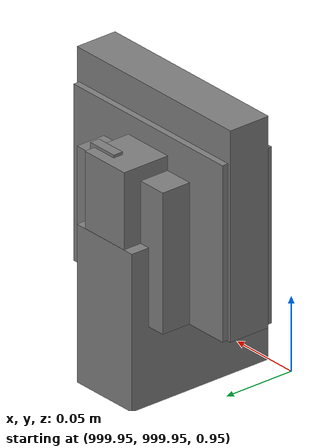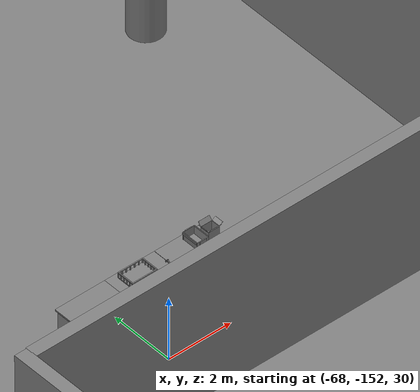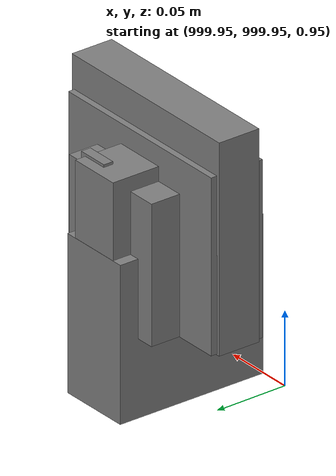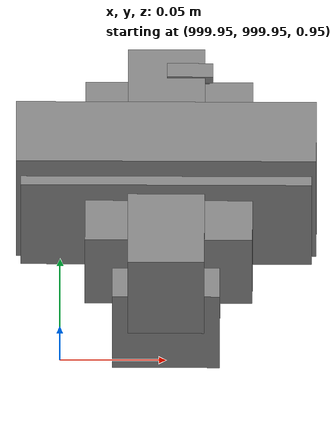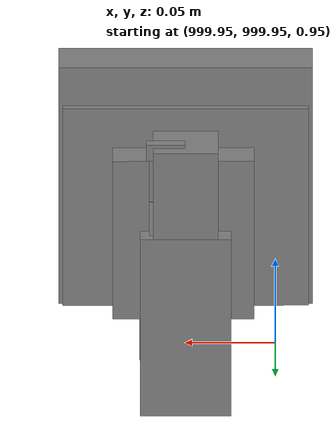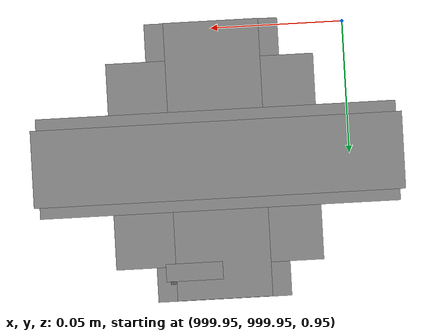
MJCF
<mujoco>
    <option gravity="0.000000000 0.000000000 -9.810000420" timestep="0.0049999999" integrator="implicitfast" density="1.225" viscosity="1.8000001e-05" noslip_iterations="10" iterations="100" sdf_iterations="50">
        <flag multiccd="disable"/>
    </option>
    <size memory="1000M"/>
    <compiler coordinate="local"/>
    <worldbody>
        <light cutoff="30" pos="0 1 1" dir="0 -1 -2"/>
        <light cutoff="30" pos="0 -1 1" dir="0 1 -2"/>
        <body pos="-64.866622925 -149.383972168 30.183746338" euler="89.999984741 89.999946594 0.000000000" name="openloong_gripper_2f85_fix_base_usda_bluebox_01">
            <geom contype="1" conaffinity="1" density="1000" type="box" material="" rgba="0.500000000 0.500000000 0.500000000 1.000000000" solimp="0.899999976 0.949999988 0.001000000" friction="1.000000000 0.005000000 0.000100000" solref="0.020000000 1.000000000" margin="0" condim="3" group="0" pos="0.276580811 0.187225342 0.000068665" quat="0.707106948 0.000077471 0.707106352 0.000077486" size="0.100000001 0.057999998 0.010000000" name="openloong_gripper_2f85_fix_base_usda_geom_AAC1E3CA_2D43_4E3D_9DE1_98EBB4260AE7"/>
            <geom contype="1" conaffinity="1" density="1000" type="box" material="" rgba="0.500000000 0.500000000 0.500000000 1.000000000" solimp="0.899999976 0.949999988 0.001000000" friction="1.000000000 0.005000000 0.000100000" solref="0.020000000 1.000000000" margin="0" condim="3" group="0" pos="0.000000000 0.002883911 0.000000000" quat="0.999999881 0.000000000 0.000000000 0.000000000" size="0.254000008 0.003000000 0.172000006" name="openloong_gripper_2f85_fix_base_usda_geom_D55BAF2E_D537_4E98_AA5A_C0CBAD89EE9B"/>
            <geom contype="1" conaffinity="1" density="1000" type="box" material="" rgba="0.500000000 0.500000000 0.500000000 1.000000000" solimp="0.899999976 0.949999988 0.001000000" friction="1.000000000 0.005000000 0.000100000" solref="0.020000000 1.000000000" margin="0" condim="3" group="0" pos="0.000000000 0.124874115 0.173484802" quat="0.999796331 0.020176515 -0.000000015 0.000000030" size="0.259999990 0.119999997 0.007000000" name="openloong_gripper_2f85_fix_base_usda_geom_A4CF5E48_4531_4FA4_BE40_7F31549701A6"/>
            <geom contype="1" conaffinity="1" density="1000" type="box" material="" rgba="0.500000000 0.500000000 0.500000000 1.000000000" solimp="0.899999976 0.949999988 0.001000000" friction="1.000000000 0.005000000 0.000100000" solref="0.020000000 1.000000000" margin="0" condim="3" group="0" pos="0.000000000 0.124874115 -0.173469543" quat="0.999796331 -0.020176545 -0.000000015 0.000000000" size="0.259999990 0.119999997 0.007000000" name="openloong_gripper_2f85_fix_base_usda_geom_648F201D_F971_4C95_ACD8_705AF6342B41"/>
            <geom contype="1" conaffinity="1" density="1000" type="box" material="" rgba="0.500000000 0.500000000 0.500000000 1.000000000" solimp="0.899999976 0.949999988 0.001000000" friction="1.000000000 0.005000000 0.000100000" solref="0.020000000 1.000000000" margin="0" condim="3" group="0" pos="0.000000000 0.214008331 0.188980103" quat="0.999912977 0.013176724 0.000000015 0.000000000" size="0.259999990 0.029999999 0.012500000" name="openloong_gripper_2f85_fix_base_usda_geom_C28A1DC3_2DEA_40CF_A69F_FFF66DAF8806"/>
            <geom contype="1" conaffinity="1" density="1000" type="box" material="" rgba="0.500000000 0.500000000 0.500000000 1.000000000" solimp="0.899999976 0.949999988 0.001000000" friction="1.000000000 0.005000000 0.000100000" solref="0.020000000 1.000000000" margin="0" condim="3" group="0" pos="-0.258361816 0.125289917 0.001876831" quat="0.702796936 -0.020792112 0.710783124 0.020769298" size="0.189999998 0.119999997 0.009000000" name="openloong_gripper_2f85_fix_base_usda_geom_D566C4FC_7F58_4C93_9524_AF336C764D6B"/>
            <geom contype="1" conaffinity="1" density="1000" type="box" material="" rgba="0.500000000 0.500000000 0.500000000 1.000000000" solimp="0.899999976 0.949999988 0.001000000" friction="1.000000000 0.005000000 0.000100000" solref="0.020000000 1.000000000" margin="0" condim="3" group="0" pos="0.000000000 0.214008331 -0.188980103" quat="0.999912977 -0.013176769 0.000000030 0.000000015" size="0.259999990 0.029999999 0.012500000" name="openloong_gripper_2f85_fix_base_usda_geom_3732F4CB_1B8E_4147_9495_9C034D38FC35"/>
            <geom contype="1" conaffinity="1" density="1000" type="box" material="" rgba="0.500000000 0.500000000 0.500000000 1.000000000" solimp="0.899999976 0.949999988 0.001000000" friction="1.000000000 0.005000000 0.000100000" solref="0.020000000 1.000000000" margin="0" condim="3" group="0" pos="-0.276611328 0.187225342 0.000068665" quat="0.707106650 0.000077441 0.707106709 0.000077456" size="0.100000001 0.057999998 0.010000000" name="openloong_gripper_2f85_fix_base_usda_geom_B8696180_449C_4EA9_A22F_BC148FA498AF"/>
            <geom contype="1" conaffinity="1" density="1000" type="box" material="" rgba="0.500000000 0.500000000 0.500000000 1.000000000" solimp="0.899999976 0.949999988 0.001000000" friction="1.000000000 0.005000000 0.000100000" solref="0.020000000 1.000000000" margin="0" condim="3" group="0" pos="0.258331299 0.125289917 0.001876831" quat="0.702851415 0.018856421 0.710823774 -0.019329369" size="0.189999998 0.119999997 0.009000000" name="openloong_gripper_2f85_fix_base_usda_geom_4657A7FD_CEA6_4D8B_822E_04B0A80431D1"/>
            <freejoint name="openloong_gripper_2f85_fix_base_usda_bluebox_01_joint"/>
            <site size="0.005000000 0.005000000 0.005000000" rgba="0.500000000 0.500000000 0.500000000 1.000000000" pos="0.000000000 0.000000000 0.000000000" quat="0.999961913 0.008726534 0.000000000 0.000000000" group="0" type="sphere" name="openloong_gripper_2f85_fix_base_usda_bluebox_01site"/>
        </body>
        <body pos="-64.496299744 -149.491867065 30.235729218" euler="0.000000000 0.000000000 89.999946594" name="openloong_gripper_2f85_fix_base_usda_cardboardbox_01">
            <geom contype="1" conaffinity="1" density="1000" type="box" material="" rgba="0.500000000 0.500000000 0.500000000 1.000000000" solimp="0.899999976 0.949999988 0.001000000" friction="1.000000000 0.005000000 0.000100000" solref="0.020000000 1.000000000" margin="0" condim="3" group="0" pos="-0.003166199 -0.004086494 0.005052090" quat="1.000000000 0.000000000 0.000000000 0.000000000" size="0.142499998 0.177500010 0.005000000" name="openloong_gripper_2f85_fix_base_usda_geom_84DA0E53_BA8C_4583_9676_169E5E470C9E"/>
            <geom contype="1" conaffinity="1" density="1000" type="box" material="" rgba="0.500000000 0.500000000 0.500000000 1.000000000" solimp="0.899999976 0.949999988 0.001000000" friction="1.000000000 0.005000000 0.000100000" solref="0.020000000 1.000000000" margin="0" condim="3" group="0" pos="-0.003166199 0.170316696 0.150570869" quat="1.000000000 0.000000000 0.000000000 0.000000000" size="0.142499998 0.005000000 0.149999991" name="openloong_gripper_2f85_fix_base_usda_geom_3E70FBA7_BEE1_44C2_A5CE_DDCC2822EDFA"/>
            <geom contype="1" conaffinity="1" density="1000" type="box" material="" rgba="0.500000000 0.500000000 0.500000000 1.000000000" solimp="0.899999976 0.949999988 0.001000000" friction="1.000000000 0.005000000 0.000100000" solref="0.020000000 1.000000000" margin="0" condim="3" group="0" pos="-0.147399902 -0.005307198 0.150570869" quat="1.000000000 0.000000000 0.000000000 0.000000000" size="0.005000000 0.177500010 0.149999991" name="openloong_gripper_2f85_fix_base_usda_geom_DB914534_1DE5_497C_883D_12D2CAA95485"/>
            <geom contype="1" conaffinity="1" density="1000" type="box" material="" rgba="0.500000000 0.500000000 0.500000000 1.000000000" solimp="0.899999976 0.949999988 0.001000000" friction="1.000000000 0.005000000 0.000100000" solref="0.020000000 1.000000000" margin="0" condim="3" group="0" pos="0.140275955 -0.005307198 0.150570869" quat="1.000000000 0.000000000 0.000000000 0.000000000" size="0.005000000 0.177500010 0.149999991" name="openloong_gripper_2f85_fix_base_usda_geom_DA9BFE70_C63B_4024_8958_CC8B7AF90D30"/>
            <geom contype="1" conaffinity="1" density="1000" type="box" material="" rgba="0.500000000 0.500000000 0.500000000 1.000000000" solimp="0.899999976 0.949999988 0.001000000" friction="1.000000000 0.005000000 0.000100000" solref="0.020000000 1.000000000" margin="0" condim="3" group="0" pos="-0.003166199 -0.181550980 0.150570869" quat="1.000000000 0.000000000 0.000000000 0.000000000" size="0.142499998 0.005000000 0.149999991" name="openloong_gripper_2f85_fix_base_usda_geom_478835E2_A4A6_4989_91CD_F45EE0FF275F"/>
            <freejoint name="openloong_gripper_2f85_fix_base_usda_cardboardbox_01_joint"/>
            <site size="0.005000000 0.005000000 0.005000000" rgba="0.500000000 0.500000000 0.500000000 1.000000000" pos="0.000000000 0.000000000 0.000000000" quat="0.999961913 0.008726535 0.000000000 0.000000000" group="0" type="sphere" name="openloong_gripper_2f85_fix_base_usda_site_04901CEA_76CC_44BE_ABA8_B5B7B0E8A06A"/>
            <body pos="0.139160156 -0.004048347 0.301930904" euler="-179.999954224 49.383502960 179.999954224" name="openloong_gripper_2f85_fix_base_usda_A1_006">
                <geom contype="1" conaffinity="1" density="1000" type="box" material="" rgba="0.500000000 0.500000000 0.500000000 1.000000000" solimp="0.899999976 0.949999988 0.001000000" friction="1.000000000 0.005000000 0.000100000" solref="0.020000000 1.000000000" margin="0" condim="3" group="0" pos="-0.071587563 0.000009537 0.001745224" quat="0.999999881 0.000000000 0.000000000 0.000000000" size="0.071249999 0.179999992 0.002500000" name="openloong_gripper_2f85_fix_base_usda_geom_DCCB20AB_166A_441B_9AE1_7E067C789CFA"/>
                <joint armature="0" stiffness="0.07" damping="0.0099999998" axis="0.000000 1.000000 0.000000" type="hinge" name="openloong_gripper_2f85_fix_base_usda_A1_006"/>
            </body>
            <body pos="-0.145902634 -0.004086494 0.301938057" euler="-180.000000000 -60.000011444 -180.000000000" name="openloong_gripper_2f85_fix_base_usda_A2_006">
                <geom contype="1" conaffinity="1" density="1000" type="box" material="" rgba="0.500000000 0.500000000 0.500000000 1.000000000" solimp="0.899999976 0.949999988 0.001000000" friction="1.000000000 0.005000000 0.000100000" solref="0.020000000 1.000000000" margin="0" condim="3" group="0" pos="0.071268082 0.000009537 0.002717972" quat="0.000002921 0.000000000 -0.000000030 0.999999881" size="0.071249999 0.179999992 0.002500000" name="openloong_gripper_2f85_fix_base_usda_geom_7DFE76B2_0EA6_4138_B76D_36E59650A3E7"/>
                <joint armature="0" stiffness="0.07" damping="0.0099999998" axis="0.000000 1.000000 0.000000" type="hinge" name="openloong_gripper_2f85_fix_base_usda_A2_006"/>
            </body>
            <body pos="-0.003385544 0.175991058 0.301930904" euler="-125.858116150 -0.000004561 0.000002331" name="openloong_gripper_2f85_fix_base_usda_B2_006">
                <geom contype="1" conaffinity="1" density="1000" type="box" material="" rgba="0.500000000 0.500000000 0.500000000 1.000000000" solimp="0.899999976 0.949999988 0.001000000" friction="1.000000000 0.005000000 0.000100000" solref="0.020000000 1.000000000" margin="0" condim="3" group="0" pos="0.000009537 -0.070939064 -0.002470016" quat="0.999614120 0.027776197 -0.000000015 0.000000030" size="0.137500003 0.064999998 0.005000000" name="openloong_gripper_2f85_fix_base_usda_geom_5808A324_3BBB_4690_9D0B_A61ADC7FFF82"/>
                <joint armature="0" stiffness="0.07" damping="0.0099999998" axis="1.000000 0.000000 0.000000" type="hinge" name="openloong_gripper_2f85_fix_base_usda_B2_006"/>
            </body>
            <body pos="-0.003385544 -0.184140205 0.301938057" euler="147.805557251 0.000000000 0.000000000" name="openloong_gripper_2f85_fix_base_usda_B1_006">
                <geom contype="1" conaffinity="1" density="1000" type="box" material="" rgba="0.500000000 0.500000000 0.500000000 1.000000000" solimp="0.899999976 0.949999988 0.001000000" friction="1.000000000 0.005000000 0.000100000" solref="0.020000000 1.000000000" margin="0" condim="3" group="0" pos="-0.000028610 0.070202351 -0.002703667" quat="0.999614179 -0.027776167 0.000000000 0.000000000" size="0.137500003 0.064999998 0.005000000" name="openloong_gripper_2f85_fix_base_usda_geom_0DFDE126_03A6_49EE_A05C_1241955E0ADD"/>
                <joint armature="0" stiffness="0.07" damping="0.0099999998" axis="1.000000 0.000000 0.000000" type="hinge" name="openloong_gripper_2f85_fix_base_usda_B1_006"/>
            </body>
        </body>
        <body pos="-65.882858276 -149.481979370 30.229999542" euler="-64.487716675 0.000000000 0.000000000" name="openloong_gripper_2f85_fix_base_usda_Barcode">
            <geom contype="1" conaffinity="1" density="1000" type="box" material="" rgba="0.500000000 0.500000000 0.500000000 1.000000000" solimp="0.899999976 0.949999988 0.001000000" friction="1.000000000 0.005000000 0.000100000" solref="0.020000000 1.000000000" margin="0" condim="3" group="0" pos="0.000000000 0.013038635 0.001419067" quat="0.000000000 0.000000000 0.000000000 1.000000119" size="0.034000002 0.010000000 0.017999999" name="openloong_gripper_2f85_fix_base_usda_geom_20BDE33C_8FF5_4CA3_AD48_03A831BEDA43"/>
            <geom contype="1" conaffinity="1" density="1000" type="box" material="" rgba="0.500000000 0.500000000 0.500000000 1.000000000" solimp="0.899999976 0.949999988 0.001000000" friction="1.000000000 0.005000000 0.000100000" solref="0.020000000 1.000000000" margin="0" condim="3" group="0" pos="0.000000000 -0.035301208 -0.007095337" quat="0.000000000 0.000000000 -0.043619365 0.999048233" size="0.028999999 0.010000000 0.020000000" name="openloong_gripper_2f85_fix_base_usda_geom_E934F188_AC9C_4E6B_913F_1982ADCC8338"/>
            <geom contype="1" conaffinity="1" density="1000" type="box" material="" rgba="0.500000000 0.500000000 0.500000000 1.000000000" solimp="0.899999976 0.949999988 0.001000000" friction="1.000000000 0.005000000 0.000100000" solref="0.020000000 1.000000000" margin="0" condim="3" group="0" pos="0.000000000 -0.043411255 -0.011749268" quat="0.922262907 0.386563420 0.000000000 0.000000000" size="0.026000001 0.010000000 0.020000000" name="openloong_gripper_2f85_fix_base_usda_geom_6D64224B_BFF9_4C6A_B530_C48531B19FD1"/>
            <geom contype="1" conaffinity="1" density="1000" type="box" material="" rgba="0.500000000 0.500000000 0.500000000 1.000000000" solimp="0.899999976 0.949999988 0.001000000" friction="1.000000000 0.005000000 0.000100000" solref="0.020000000 1.000000000" margin="0" condim="3" group="0" pos="0.000000000 -0.016967773 -0.031860352" quat="0.000000000 0.000000000 0.000000000 1.000000119" size="0.008000000 0.010000000 0.013000000" name="openloong_gripper_2f85_fix_base_usda_geom_8D771EC2_D005_4FB0_8195_F877CE7768B3"/>
            <geom contype="1" conaffinity="1" density="1000" type="box" material="" rgba="0.500000000 0.500000000 0.500000000 1.000000000" solimp="0.899999976 0.949999988 0.001000000" friction="1.000000000 0.005000000 0.000100000" solref="0.020000000 1.000000000" margin="0" condim="3" group="0" pos="0.000000000 -0.001869202 0.000312805" quat="0.953716993 0.300705761 0.000000000 0.000000000" size="0.032000002 0.010000000 0.018999999" name="openloong_gripper_2f85_fix_base_usda_geom_EDCC3E9D_28EE_4B8C_B0C6_B25672BDF8DB"/>
            <geom contype="1" conaffinity="1" density="1000" type="box" material="" rgba="0.500000000 0.500000000 0.500000000 1.000000000" solimp="0.899999976 0.949999988 0.001000000" friction="1.000000000 0.005000000 0.000100000" solref="0.020000000 1.000000000" margin="0" condim="3" group="0" pos="0.000000000 -0.019531250 -0.003173828" quat="0.953716993 0.300705761 0.000000000 0.000000000" size="0.030999999 0.010000000 0.020000000" name="openloong_gripper_2f85_fix_base_usda_geom_F894D73B_13C1_4A47_928F_86173EECEA3A"/>
            <geom contype="1" conaffinity="1" density="1000" type="box" material="" rgba="0.500000000 0.500000000 0.500000000 1.000000000" solimp="0.899999976 0.949999988 0.001000000" friction="1.000000000 0.005000000 0.000100000" solref="0.020000000 1.000000000" margin="0" condim="3" group="0" pos="0.000000000 -0.035301208 -0.007095337" quat="0.953716993 0.300705761 0.000000000 0.000000000" size="0.028999999 0.010000000 0.020000000" name="openloong_gripper_2f85_fix_base_usda_geom_9F2D974F_2C97_44F7_A427_160EA784A93F"/>
            <geom contype="1" conaffinity="1" density="1000" type="box" material="" rgba="0.500000000 0.500000000 0.500000000 1.000000000" solimp="0.899999976 0.949999988 0.001000000" friction="1.000000000 0.005000000 0.000100000" solref="0.020000000 1.000000000" margin="0" condim="3" group="0" pos="0.000000000 -0.042617798 -0.071121216" quat="0.000000000 0.000000000 0.000000000 1.000000119" size="0.013000000 0.021000000 0.059999999" name="openloong_gripper_2f85_fix_base_usda_geom_B789C8BA_E6B9_4D05_B97E_313FE6CA87D8"/>
            <freejoint name="openloong_gripper_2f85_fix_base_usda_Barcode_joint"/>
            <site size="0.005000000 0.005000000 0.005000000" rgba="0.500000000 0.500000000 0.500000000 1.000000000" pos="0.000000000 0.000000000 0.000000000" quat="1.000000000 0.000000000 0.000000000 0.000000000" group="0" type="sphere" name="openloong_gripper_2f85_fix_base_usda_Barcode_site"/>
        </body>
        <body pos="-66.745018005 -149.392349243 30.184000015" euler="0.000000000 0.000000000 89.999946594" name="[22331067954631]_Basket_01">
            <geom contype="1" conaffinity="1" density="1000" type="box" material="" rgba="0.500000000 0.500000000 0.500000000 1.000000000" solimp="0.899999976 0.949999988 0.001000000" friction="1.000000000 0.005000000 0.000100000" solref="0.020000000 1.000000000" margin="0" condim="3" group="0" pos="-0.052425385 0.389207840 0.089787483" quat="0.707107008 0.000000000 0.000000000 0.707106411" size="0.014249999 0.014249999 0.059999999" name="[22331067954631]_geom_372F8F55_29F8_4B65_821C_99FC978E790E"/>
            <geom contype="1" conaffinity="1" density="1000" type="box" material="" rgba="0.500000000 0.500000000 0.500000000 1.000000000" solimp="0.899999976 0.949999988 0.001000000" friction="1.000000000 0.005000000 0.000100000" solref="0.020000000 1.000000000" margin="0" condim="3" group="0" pos="0.264015198 -0.133043289 0.089787483" quat="0.707107008 0.000000000 0.000000000 0.707106411" size="0.014249999 0.014249999 0.059999999" name="[22331067954631]_geom_2C98D3C3_9308_4C7B_9DC2_C32A3E3A1406"/>
            <geom contype="1" conaffinity="1" density="1000" type="box" material="" rgba="0.500000000 0.500000000 0.500000000 1.000000000" solimp="0.899999976 0.949999988 0.001000000" friction="1.000000000 0.005000000 0.000100000" solref="0.020000000 1.000000000" margin="0" condim="3" group="0" pos="-0.264015198 -0.265548706 0.089793205" quat="0.707107008 0.000000000 0.000000000 0.707106411" size="0.014249999 0.014249999 0.059999999" name="[22331067954631]_geom_627E3F60_9ADC_4448_A962_6EAD907485BC"/>
            <geom contype="1" conaffinity="1" density="1000" type="box" material="" rgba="0.500000000 0.500000000 0.500000000 1.000000000" solimp="0.899999976 0.949999988 0.001000000" friction="1.000000000 0.005000000 0.000100000" solref="0.020000000 1.000000000" margin="0" condim="3" group="0" pos="-0.160263062 -0.389322281 0.089793205" quat="0.707107008 0.000000000 0.000000000 0.707106411" size="0.014249999 0.014249999 0.059999999" name="[22331067954631]_geom_A6BCBD05_C14F_4264_8921_6E63F2B2FB4E"/>
            <geom contype="1" conaffinity="1" density="1000" type="box" material="" rgba="0.500000000 0.500000000 0.500000000 1.000000000" solimp="0.899999976 0.949999988 0.001000000" friction="1.000000000 0.005000000 0.000100000" solref="0.020000000 1.000000000" margin="0" condim="3" group="0" pos="0.162265778 -0.389322281 0.089787483" quat="0.707107008 0.000000000 0.000000000 0.707106411" size="0.014249999 0.014249999 0.059999999" name="[22331067954631]_geom_88D0BC4F_DCBC_4127_BBE0_27085A7E6378"/>
            <geom contype="1" conaffinity="1" density="1000" type="box" material="" rgba="0.500000000 0.500000000 0.500000000 1.000000000" solimp="0.899999976 0.949999988 0.001000000" friction="1.000000000 0.005000000 0.000100000" solref="0.020000000 1.000000000" margin="0" condim="3" group="0" pos="0.264015198 0.389207840 0.089787483" quat="0.707107008 0.000000000 0.000000000 0.707106411" size="0.014249999 0.014249999 0.059999999" name="[22331067954631]_geom_03E9AAED_4344_4B3F_B6B3_4670F33155D9"/>
            <geom contype="1" conaffinity="1" density="1000" type="box" material="" rgba="0.500000000 0.500000000 0.500000000 1.000000000" solimp="0.899999976 0.949999988 0.001000000" friction="1.000000000 0.005000000 0.000100000" solref="0.020000000 1.000000000" margin="0" condim="3" group="0" pos="-0.264015198 -0.133043289 0.089793205" quat="0.707107008 0.000000000 0.000000000 0.707106411" size="0.014249999 0.014249999 0.059999999" name="[22331067954631]_geom_C095B78B_9457_420F_BDD0_B9B6352EA4B4"/>
            <geom contype="1" conaffinity="1" density="1000" type="box" material="" rgba="0.500000000 0.500000000 0.500000000 1.000000000" solimp="0.899999976 0.949999988 0.001000000" friction="1.000000000 0.005000000 0.000100000" solref="0.020000000 1.000000000" margin="0" condim="3" group="0" pos="-0.264026642 0.269256592 0.089793205" quat="0.707107008 0.000000000 0.000000000 0.707106411" size="0.014249999 0.014249999 0.059999999" name="[22331067954631]_geom_56427D7A_06BB_45B4_BD2A_7AC112B063A5"/>
            <geom contype="1" conaffinity="1" density="1000" type="box" material="" rgba="0.500000000 0.500000000 0.500000000 1.000000000" solimp="0.899999976 0.949999988 0.001000000" friction="1.000000000 0.005000000 0.000100000" solref="0.020000000 1.000000000" margin="0" condim="3" group="0" pos="0.054462433 0.389207840 0.089787483" quat="0.707107008 0.000000000 0.000000000 0.707106411" size="0.014249999 0.014249999 0.059999999" name="[22331067954631]_geom_5F412075_EB41_44AF_A209_5B12B90DD1B2"/>
            <geom contype="1" conaffinity="1" density="1000" type="box" material="" rgba="0.500000000 0.500000000 0.500000000 1.000000000" solimp="0.899999976 0.949999988 0.001000000" friction="1.000000000 0.005000000 0.000100000" solref="0.020000000 1.000000000" margin="0" condim="3" group="0" pos="0.054462433 -0.389322281 0.089787483" quat="0.707107008 0.000000000 0.000000000 0.707106411" size="0.014249999 0.014249999 0.059999999" name="[22331067954631]_geom_8072303F_B7AD_402E_88F0_E76C2CCEF348"/>
            <geom contype="1" conaffinity="1" density="1000" type="box" material="" rgba="0.500000000 0.500000000 0.500000000 1.000000000" solimp="0.899999976 0.949999988 0.001000000" friction="1.000000000 0.005000000 0.000100000" solref="0.020000000 1.000000000" margin="0" condim="3" group="0" pos="0.264015198 0.269256592 0.089793205" quat="0.707107008 0.000000000 0.000000000 0.707106411" size="0.014249999 0.014249999 0.059999999" name="[22331067954631]_geom_B71E6CC1_6811_4833_B0BF_8202A32C140C"/>
            <geom contype="1" conaffinity="1" density="1000" type="box" material="" rgba="0.500000000 0.500000000 0.500000000 1.000000000" solimp="0.899999976 0.949999988 0.001000000" friction="1.000000000 0.005000000 0.000100000" solref="0.020000000 1.000000000" margin="0" condim="3" group="0" pos="0.264015198 -0.389322281 0.089787483" quat="0.707107008 0.000000000 0.000000000 0.707106411" size="0.014249999 0.014249999 0.059999999" name="[22331067954631]_geom_679D1C88_0D20_4717_B1A9_88355EFEA214"/>
            <geom contype="1" conaffinity="1" density="1000" type="box" material="" rgba="0.500000000 0.500000000 0.500000000 1.000000000" solimp="0.899999976 0.949999988 0.001000000" friction="1.000000000 0.005000000 0.000100000" solref="0.020000000 1.000000000" margin="0" condim="3" group="0" pos="0.000000000 0.000000000 0.015998840" quat="0.707107008 0.000000000 0.000000000 0.707106411" size="0.403499991 0.279000014 0.015750000" name="[22331067954631]_geom_0EE25079_0F31_4152_9256_7DCA2FBECE62"/>
            <geom contype="1" conaffinity="1" density="1000" type="box" material="" rgba="0.500000000 0.500000000 0.500000000 1.000000000" solimp="0.899999976 0.949999988 0.001000000" friction="1.000000000 0.005000000 0.000100000" solref="0.020000000 1.000000000" margin="0" condim="3" group="0" pos="0.000000000 -0.389476776 0.163619041" quat="0.707107008 0.000000000 0.000000000 0.707106411" size="0.015000000 0.277500004 0.015750000" name="[22331067954631]_geom_6706AF62_5A95_4CD7_879E_10D6F90FC7B8"/>
            <geom contype="1" conaffinity="1" density="1000" type="box" material="" rgba="0.500000000 0.500000000 0.500000000 1.000000000" solimp="0.899999976 0.949999988 0.001000000" friction="1.000000000 0.005000000 0.000100000" solref="0.020000000 1.000000000" margin="0" condim="3" group="0" pos="0.162265778 0.389207840 0.089787483" quat="0.707107008 0.000000000 0.000000000 0.707106411" size="0.014249999 0.014249999 0.059999999" name="[22331067954631]_geom_33716F3F_0E05_4FB8_A4BD_563988F0B770"/>
            <geom contype="1" conaffinity="1" density="1000" type="box" material="" rgba="0.500000000 0.500000000 0.500000000 1.000000000" solimp="0.899999976 0.949999988 0.001000000" friction="1.000000000 0.005000000 0.000100000" solref="0.020000000 1.000000000" margin="0" condim="3" group="0" pos="0.000000000 0.389471054 0.163619041" quat="0.707107008 0.000000000 0.000000000 0.707106411" size="0.015000000 0.277500004 0.015750000" name="[22331067954631]_geom_89CEE53A_89EC_4EB1_B5C6_A976B7A4FE9E"/>
            <geom contype="1" conaffinity="1" density="1000" type="box" material="" rgba="0.500000000 0.500000000 0.500000000 1.000000000" solimp="0.899999976 0.949999988 0.001000000" friction="1.000000000 0.005000000 0.000100000" solref="0.020000000 1.000000000" margin="0" condim="3" group="0" pos="-0.263511658 0.000000000 0.163619041" quat="0.707107008 0.000000000 0.000000000 0.707106411" size="0.403499991 0.015000000 0.015750000" name="[22331067954631]_geom_1D532EE1_D747_4941_94C0_1F5D3C9CB638"/>
            <geom contype="1" conaffinity="1" density="1000" type="box" material="" rgba="0.500000000 0.500000000 0.500000000 1.000000000" solimp="0.899999976 0.949999988 0.001000000" friction="1.000000000 0.005000000 0.000100000" solref="0.020000000 1.000000000" margin="0" condim="3" group="0" pos="-0.264015198 0.141334534 0.089793205" quat="0.707107008 0.000000000 0.000000000 0.707106411" size="0.014249999 0.014249999 0.059999999" name="[22331067954631]_geom_79DDBA2C_97E1_4CBE_9E57_64E3517C618A"/>
            <geom contype="1" conaffinity="1" density="1000" type="box" material="" rgba="0.500000000 0.500000000 0.500000000 1.000000000" solimp="0.899999976 0.949999988 0.001000000" friction="1.000000000 0.005000000 0.000100000" solref="0.020000000 1.000000000" margin="0" condim="3" group="0" pos="0.264015198 -0.265548706 0.089787483" quat="0.707107008 0.000000000 0.000000000 0.707106411" size="0.014249999 0.014249999 0.059999999" name="[22331067954631]_geom_69350253_4617_458C_973F_34EAC6892CB9"/>
            <geom contype="1" conaffinity="1" density="1000" type="box" material="" rgba="0.500000000 0.500000000 0.500000000 1.000000000" solimp="0.899999976 0.949999988 0.001000000" friction="1.000000000 0.005000000 0.000100000" solref="0.020000000 1.000000000" margin="0" condim="3" group="0" pos="-0.160263062 0.389207840 0.089787483" quat="0.707107008 0.000000000 0.000000000 0.707106411" size="0.014249999 0.014249999 0.059999999" name="[22331067954631]_geom_B4CDA68F_A0E0_42FD_97C7_B89A551B8E1C"/>
            <geom contype="1" conaffinity="1" density="1000" type="box" material="" rgba="0.500000000 0.500000000 0.500000000 1.000000000" solimp="0.899999976 0.949999988 0.001000000" friction="1.000000000 0.005000000 0.000100000" solref="0.020000000 1.000000000" margin="0" condim="3" group="0" pos="-0.052425385 -0.389322281 0.089787483" quat="0.707107008 0.000000000 0.000000000 0.707106411" size="0.014249999 0.014249999 0.059999999" name="[22331067954631]_geom_76AADC4E_5DA7_49B0_A781_E2E67ED60953"/>
            <geom contype="1" conaffinity="1" density="1000" type="box" material="" rgba="0.500000000 0.500000000 0.500000000 1.000000000" solimp="0.899999976 0.949999988 0.001000000" friction="1.000000000 0.005000000 0.000100000" solref="0.020000000 1.000000000" margin="0" condim="3" group="0" pos="-0.264026642 -0.389322281 0.089793205" quat="0.707107008 0.000000000 0.000000000 0.707106411" size="0.014249999 0.014249999 0.059999999" name="[22331067954631]_geom_F12EEA34_68D9_41BA_A0C2_2E5FD18E14E4"/>
            <geom contype="1" conaffinity="1" density="1000" type="box" material="" rgba="0.500000000 0.500000000 0.500000000 1.000000000" solimp="0.899999976 0.949999988 0.001000000" friction="1.000000000 0.005000000 0.000100000" solref="0.020000000 1.000000000" margin="0" condim="3" group="0" pos="0.264015198 0.141334534 0.089787483" quat="0.707107008 0.000000000 0.000000000 0.707106411" size="0.014249999 0.014249999 0.059999999" name="[22331067954631]_geom_E18C29CE_F46B_4EC3_8AC7_CB2198214E72"/>
            <geom contype="1" conaffinity="1" density="1000" type="box" material="" rgba="0.500000000 0.500000000 0.500000000 1.000000000" solimp="0.899999976 0.949999988 0.001000000" friction="1.000000000 0.005000000 0.000100000" solref="0.020000000 1.000000000" margin="0" condim="3" group="0" pos="-0.264015198 0.389207840 0.089793205" quat="0.707107008 0.000000000 0.000000000 0.707106411" size="0.014249999 0.014249999 0.059999999" name="[22331067954631]_geom_300BAC77_DC45_4D27_B1FE_45971231CE46"/>
            <geom contype="1" conaffinity="1" density="1000" type="box" material="" rgba="0.500000000 0.500000000 0.500000000 1.000000000" solimp="0.899999976 0.949999988 0.001000000" friction="1.000000000 0.005000000 0.000100000" solref="0.020000000 1.000000000" margin="0" condim="3" group="0" pos="0.264015198 0.004480362 0.089787483" quat="0.707107008 0.000000000 0.000000000 0.707106411" size="0.014249999 0.014249999 0.059999999" name="[22331067954631]_geom_858BF782_6CC0_4183_8AD1_1628A61B7BD5"/>
            <geom contype="1" conaffinity="1" density="1000" type="box" material="" rgba="0.500000000 0.500000000 0.500000000 1.000000000" solimp="0.899999976 0.949999988 0.001000000" friction="1.000000000 0.005000000 0.000100000" solref="0.020000000 1.000000000" margin="0" condim="3" group="0" pos="0.263694763 -0.000011444 0.163619041" quat="0.707107008 0.000000000 0.000000000 0.707106411" size="0.403499991 0.015000000 0.015750000" name="[22331067954631]_geom_E34F152E_3194_4286_8CF2_F95334E852E3"/>
            <geom contype="1" conaffinity="1" density="1000" type="box" material="" rgba="0.500000000 0.500000000 0.500000000 1.000000000" solimp="0.899999976 0.949999988 0.001000000" friction="1.000000000 0.005000000 0.000100000" solref="0.020000000 1.000000000" margin="0" condim="3" group="0" pos="-0.264015198 0.004480362 0.089793205" quat="0.707107008 0.000000000 0.000000000 0.707106411" size="0.014249999 0.014249999 0.059999999" name="[22331067954631]_geom_554AB3C2_5131_44A9_9DD2_EE64A7A1276C"/>
            <freejoint name="[22331067954631]_joint_0418F077_8496_4532_BD9D_3DDF9D55D6ED"/>
        </body>
        <body pos="0.000000000 0.000000000 0.000000000" euler="0.000000000 0.000000000 0.000000000" name="Static Objects_Static Objects">
            <geom contype="1" conaffinity="1" density="1000" type="box" material="" rgba="0.500000000 0.500000000 0.500000000 1.000000000" solimp="0.899999976 0.949999988 0.001000000" friction="1.000000000 0.005000000 0.000100000" solref="0.020000000 1.000000000" margin="0" condim="3" group="0" pos="-67.544113159 -149.365814209 29.727830887" quat="0.500000417 0.499999970 0.499999553 0.499999970" size="0.381000012 0.319999993 0.041000001" name="Static Objects_geom_85A52478_AFD8_43ED_AAE5_3619727F98C6"/>
            <geom contype="1" conaffinity="1" density="1000" type="box" material="" rgba="0.500000000 0.500000000 0.500000000 1.000000000" solimp="0.899999976 0.949999988 0.001000000" friction="1.000000000 0.005000000 0.000100000" solref="0.020000000 1.000000000" margin="0" condim="3" group="0" pos="-68.239501953 -149.365814209 30.086868286" quat="0.500000417 0.499999970 0.499999553 0.499999970" size="0.370999992 0.039500002 0.745000005" name="Static Objects_geom_4C1AB92D_C229_41C4_A4F8_D18D66D5CC24"/>
            <geom contype="1" conaffinity="1" density="1000" type="box" material="" rgba="0.500000000 0.500000000 0.500000000 1.000000000" solimp="0.899999976 0.949999988 0.001000000" friction="1.000000000 0.005000000 0.000100000" solref="0.020000000 1.000000000" margin="0" condim="3" group="0" pos="-68.239501953 -149.365814209 30.147235870" quat="0.500000417 0.499999970 0.499999553 0.499999970" size="0.400000006 0.022000000 0.800000012" name="Static Objects_geom_CC9BA588_EE3E_4B10_98E7_9AE918A2B498"/>
            <geom contype="1" conaffinity="1" density="1000" type="box" material="" rgba="0.500000000 0.500000000 0.500000000 1.000000000" solimp="0.899999976 0.949999988 0.001000000" friction="1.000000000 0.005000000 0.000100000" solref="0.020000000 1.000000000" margin="0" condim="3" group="0" pos="-68.934890747 -149.365814209 29.727830887" quat="0.500000417 0.499999970 0.499999553 0.499999970" size="0.381000012 0.319999993 0.041000001" name="Static Objects_geom_58B70B20_1302_4EAE_8E80_65FBA9BE8970"/>
            <geom contype="1" conaffinity="1" density="1000" type="box" material="" rgba="0.500000000 0.500000000 0.500000000 1.000000000" solimp="0.899999976 0.949999988 0.001000000" friction="1.000000000 0.005000000 0.000100000" solref="0.020000000 1.000000000" margin="0" condim="3" group="0" pos="-68.239501953 -149.365814209 29.561563492" quat="0.500000417 0.499999970 0.499999553 0.499999970" size="0.020000000 0.022000000 0.660000026" name="Static Objects_geom_AD3B1E69_0564_4C71_B1E6_1272AA6D3C24"/>
            <geom contype="1" conaffinity="1" density="1000" type="box" material="" rgba="0.500000000 0.500000000 0.500000000 1.000000000" solimp="0.899999976 0.949999988 0.001000000" friction="1.000000000 0.005000000 0.000100000" solref="0.020000000 1.000000000" margin="0" condim="3" group="0" pos="-65.945671082 -149.365814209 29.727830887" quat="0.500000417 0.499999970 0.499999553 0.499999970" size="0.381000012 0.319999993 0.041000001" name="Static Objects_geom_C967A603_597A_4EED_9D41_FB553733F949"/>
            <geom contype="1" conaffinity="1" density="1000" type="box" material="" rgba="0.500000000 0.500000000 0.500000000 1.000000000" solimp="0.899999976 0.949999988 0.001000000" friction="1.000000000 0.005000000 0.000100000" solref="0.020000000 1.000000000" margin="0" condim="3" group="0" pos="-66.641059875 -149.365814209 30.086868286" quat="0.500000417 0.499999970 0.499999553 0.499999970" size="0.370999992 0.039500002 0.745000005" name="Static Objects_geom_656D3C4C_2140_4092_93A6_C91B3DFAF88B"/>
            <geom contype="1" conaffinity="1" density="1000" type="box" material="" rgba="0.500000000 0.500000000 0.500000000 1.000000000" solimp="0.899999976 0.949999988 0.001000000" friction="1.000000000 0.005000000 0.000100000" solref="0.020000000 1.000000000" margin="0" condim="3" group="0" pos="-66.641059875 -149.365814209 30.147235870" quat="0.500000417 0.499999970 0.499999553 0.499999970" size="0.400000006 0.022000000 0.800000012" name="Static Objects_geom_8917C31B_1B05_4473_88D1_0A6CC6B7662A"/>
            <geom contype="1" conaffinity="1" density="1000" type="box" material="" rgba="0.500000000 0.500000000 0.500000000 1.000000000" solimp="0.899999976 0.949999988 0.001000000" friction="1.000000000 0.005000000 0.000100000" solref="0.020000000 1.000000000" margin="0" condim="3" group="0" pos="-67.336448669 -149.365814209 29.727830887" quat="0.500000417 0.499999970 0.499999553 0.499999970" size="0.381000012 0.319999993 0.041000001" name="Static Objects_geom_EDFDF1FA_C496_4C25_9AA5_FC00CE8A8DED"/>
            <geom contype="1" conaffinity="1" density="1000" type="box" material="" rgba="0.500000000 0.500000000 0.500000000 1.000000000" solimp="0.899999976 0.949999988 0.001000000" friction="1.000000000 0.005000000 0.000100000" solref="0.020000000 1.000000000" margin="0" condim="3" group="0" pos="-66.641059875 -149.365814209 29.561563492" quat="0.500000417 0.499999970 0.499999553 0.499999970" size="0.020000000 0.022000000 0.660000026" name="Static Objects_geom_69242529_9603_40E4_BF4C_F34E0CBDEE64"/>
            <geom contype="1" conaffinity="1" density="1000" type="box" material="" rgba="0.500000000 0.500000000 0.500000000 1.000000000" solimp="0.899999976 0.949999988 0.001000000" friction="1.000000000 0.005000000 0.000100000" solref="0.020000000 1.000000000" margin="0" condim="3" group="0" pos="-64.338577271 -149.365814209 29.727830887" quat="0.500000417 0.499999970 0.499999553 0.499999970" size="0.381000012 0.319999993 0.041000001" name="Static Objects_geom_29095B1A_A723_49D4_B005_9738D8073274"/>
            <geom contype="1" conaffinity="1" density="1000" type="box" material="" rgba="0.500000000 0.500000000 0.500000000 1.000000000" solimp="0.899999976 0.949999988 0.001000000" friction="1.000000000 0.005000000 0.000100000" solref="0.020000000 1.000000000" margin="0" condim="3" group="0" pos="-65.033966064 -149.365814209 30.086868286" quat="0.500000417 0.499999970 0.499999553 0.499999970" size="0.370999992 0.039500002 0.745000005" name="Static Objects_geom_569F5D43_EF20_49CE_A63D_0CBA5D37369B"/>
            <geom contype="1" conaffinity="1" density="1000" type="box" material="" rgba="0.500000000 0.500000000 0.500000000 1.000000000" solimp="0.899999976 0.949999988 0.001000000" friction="1.000000000 0.005000000 0.000100000" solref="0.020000000 1.000000000" margin="0" condim="3" group="0" pos="-65.033966064 -149.365814209 30.147235870" quat="0.500000417 0.499999970 0.499999553 0.499999970" size="0.400000006 0.022000000 0.800000012" name="Static Objects_geom_84295D73_5F5A_45B7_87D6_FD2FE826A985"/>
            <geom contype="1" conaffinity="1" density="1000" type="box" material="" rgba="0.500000000 0.500000000 0.500000000 1.000000000" solimp="0.899999976 0.949999988 0.001000000" friction="1.000000000 0.005000000 0.000100000" solref="0.020000000 1.000000000" margin="0" condim="3" group="0" pos="-65.729354858 -149.365814209 29.727830887" quat="0.500000417 0.499999970 0.499999553 0.499999970" size="0.381000012 0.319999993 0.041000001" name="Static Objects_geom_FD166744_7B61_473B_8CCE_040EFE018BCD"/>
            <geom contype="1" conaffinity="1" density="1000" type="box" material="" rgba="0.500000000 0.500000000 0.500000000 1.000000000" solimp="0.899999976 0.949999988 0.001000000" friction="1.000000000 0.005000000 0.000100000" solref="0.020000000 1.000000000" margin="0" condim="3" group="0" pos="-65.033966064 -149.365814209 29.561563492" quat="0.500000417 0.499999970 0.499999553 0.499999970" size="0.020000000 0.022000000 0.660000026" name="Static Objects_geom_E200B734_8BDE_4665_A00B_E3E13CE2B1D3"/>
            <geom contype="1" conaffinity="1" density="1000" type="box" material="" rgba="0.500000000 0.500000000 0.500000000 1.000000000" solimp="0.899999976 0.949999988 0.001000000" friction="1.000000000 0.005000000 0.000100000" solref="0.020000000 1.000000000" margin="0" condim="3" group="0" pos="-61.754566193 -137.853729248 33.906845093" quat="0.707107067 0.000000000 0.000000000 0.707106471" size="0.759999990 0.759999990 4.500000000" name="Static Objects_geom_EB06D881_96C2_4DC4_B95D_5605EFC3B20F"/>
            <geom contype="1" conaffinity="1" density="1000" type="box" material="" rgba="0.500000000 0.500000000 0.500000000 1.000000000" solimp="0.899999976 0.949999988 0.001000000" friction="1.000000000 0.005000000 0.000100000" solref="0.020000000 1.000000000" margin="0" condim="3" group="0" pos="-57.511135101 -144.927108765 31.707921982" quat="1.000000000 0.000000000 0.000000000 0.000000000" size="0.200000003 8.000000000 2.299999952" name="Static Objects_geom_2C730494_31E6_4839_9E64_CFF224B78F1D"/>
            <geom contype="1" conaffinity="1" density="1000" type="box" material="" rgba="0.500000000 0.500000000 0.500000000 1.000000000" solimp="0.899999976 0.949999988 0.001000000" friction="1.000000000 0.005000000 0.000100000" solref="0.020000000 1.000000000" margin="0" condim="3" group="0" pos="-80.517646790 -157.574050903 31.688196182" quat="0.707107067 0.000000000 0.000000000 0.707106471" size="0.600000024 0.600000024 2.299999952" name="Static Objects_geom_6E1E41AE_3C4C_46C8_9C5B_BC005288BAB1"/>
            <geom contype="1" conaffinity="1" density="1000" type="box" material="" rgba="0.500000000 0.500000000 0.500000000 1.000000000" solimp="0.899999976 0.949999988 0.001000000" friction="1.000000000 0.005000000 0.000100000" solref="0.020000000 1.000000000" margin="0" condim="3" group="0" pos="-80.711044312 -147.414932251 31.666158676" quat="1.000000000 0.000000000 0.000000000 0.000000000" size="0.200000003 10.000000000 2.299999952" name="Static Objects_geom_4BBF2F43_8938_4E10_88C3_DE2A9B910722"/>
            <geom contype="1" conaffinity="1" density="1000" type="box" material="" rgba="0.500000000 0.500000000 0.500000000 1.000000000" solimp="0.899999976 0.949999988 0.001000000" friction="1.000000000 0.005000000 0.000100000" solref="0.020000000 1.000000000" margin="0" condim="3" group="0" pos="-57.687217712 -137.434692383 31.688196182" quat="0.707107067 0.000000000 0.000000000 0.707106471" size="0.600000024 0.600000024 2.299999952" name="Static Objects_geom_FBFAEF1F_D150_4334_9EB5_AC29D1EB3553"/>
            <geom contype="1" conaffinity="1" density="1000" type="box" material="" rgba="0.500000000 0.500000000 0.500000000 1.000000000" solimp="0.899999976 0.949999988 0.001000000" friction="1.000000000 0.005000000 0.000100000" solref="0.020000000 1.000000000" margin="0" condim="3" group="0" pos="-69.537033081 -140.263229370 31.714921951" quat="0.707107067 0.000000000 0.000000000 0.707106471" size="0.759999990 4.500000000 2.299999952" name="Static Objects_geom_4A375FA1_2D63_4E24_8EB9_A60FA57B4066"/>
            <geom contype="1" conaffinity="1" density="1000" type="box" material="" rgba="0.500000000 0.500000000 0.500000000 1.000000000" solimp="0.899999976 0.949999988 0.001000000" friction="1.000000000 0.005000000 0.000100000" solref="0.020000000 1.000000000" margin="0" condim="3" group="0" pos="-80.073638916 -137.853713989 33.906845093" quat="0.707107067 0.000000000 0.000000000 0.707106471" size="0.759999990 0.759999990 4.500000000" name="Static Objects_geom_603D79AD_0F7B_4749_B493_E2F55F91F1E3"/>
            <geom contype="1" conaffinity="1" density="1000" type="box" material="" rgba="0.500000000 0.500000000 0.500000000 1.000000000" solimp="0.899999976 0.949999988 0.001000000" friction="1.000000000 0.005000000 0.000100000" solref="0.020000000 1.000000000" margin="0" condim="3" group="0" pos="-73.406707764 -155.734664917 31.707921982" quat="1.000000000 0.000000000 0.000000000 0.000000000" size="0.200000003 3.000000000 2.299999952" name="Static Objects_geom_DE6E0B52_A5CF_4AE7_AA35_72C8319DC70F"/>
            <geom contype="1" conaffinity="1" density="1000" type="box" material="" rgba="0.500000000 0.500000000 0.500000000 1.000000000" solimp="0.899999976 0.949999988 0.001000000" friction="1.000000000 0.005000000 0.000100000" solref="0.020000000 1.000000000" margin="0" condim="3" group="0" pos="-68.497543335 -137.448257446 31.707921982" quat="0.707107067 0.000000000 0.000000000 0.707106471" size="0.200000003 14.000000000 2.299999952" name="Static Objects_geom_11CB6DBF_AD4F_443C_ACF3_2AC0697E7F09"/>
            <geom contype="1" conaffinity="1" density="1000" type="cylinder" material="" rgba="0.500000000 0.500000000 0.500000000 1.000000000" solimp="0.899999976 0.949999988 0.001000000" friction="1.000000000 0.005000000 0.000100000" solref="0.020000000 1.000000000" margin="0" condim="3" group="0" pos="-68.868522644 -142.134506226 31.711090088" quat="0.707107067 0.000000000 0.000000000 0.707106471" size="0.509999990 2.299999952 1.000000000" name="Static Objects_geom_61BBB259_57DD_4591_ACF9_DDA00241D0A9"/>
            <geom contype="1" conaffinity="1" density="1000" type="plane" material="" rgba="0.500000000 0.500000000 0.500000000 1.000000000" solimp="0.899999976 0.949999988 0.001000000" friction="1.000000000 0.005000000 0.000100000" solref="0.020000000 1.000000000" margin="0" condim="3" group="0" pos="-72.873703003 -147.131927490 29.409669876" quat="1.000000000 0.000000000 0.000000000 0.000000000" size="18.000000000 14.000000000 1.000000000" name="Static Objects_geom_9310F632_E7A5_4075_9BE3_F03459D12715"/>
            <geom contype="1" conaffinity="1" density="1000" type="box" material="" rgba="0.500000000 0.500000000 0.500000000 1.000000000" solimp="0.899999976 0.949999988 0.001000000" friction="1.000000000 0.005000000 0.000100000" solref="0.020000000 1.000000000" margin="0" condim="3" group="0" pos="-79.943580627 -157.782272339 31.707921982" quat="0.707107067 0.000000000 0.000000000 0.707106471" size="0.200000003 7.000000000 2.299999952" name="Static Objects_geom_C7281DC0_99FE_49E4_A3D8_68C2C4F80343"/>
            <geom contype="1" conaffinity="1" density="1000" type="box" material="" rgba="0.500000000 0.500000000 0.500000000 1.000000000" solimp="0.899999976 0.949999988 0.001000000" friction="1.000000000 0.005000000 0.000100000" solref="0.020000000 1.000000000" margin="0" condim="3" group="0" pos="-65.421028137 -152.903442383 31.707921982" quat="0.707107067 0.000000000 0.000000000 0.707106471" size="0.200000003 7.800000191 2.299999952" name="Static Objects_geom_BFDAD879_DDC0_4DA7_B5C5_1F4726E369B2"/>
            <geom contype="1" conaffinity="1" density="1000" type="box" material="" rgba="0.500000000 0.500000000 0.500000000 1.000000000" solimp="0.899999976 0.949999988 0.001000000" friction="1.000000000 0.005000000 0.000100000" solref="0.020000000 1.000000000" margin="0" condim="3" group="0" pos="-74.776908875 -149.964416504 31.688196182" quat="1.000000000 0.000000000 0.000000000 0.000000000" size="0.600000024 0.409999996 2.299999952" name="Static Objects_geom_3D689739_A30D_4DBC_BD02_A4979CD95FB3"/>
            <geom contype="1" conaffinity="1" density="1000" type="cylinder" material="" rgba="0.500000000 0.500000000 0.500000000 1.000000000" solimp="0.899999976 0.949999988 0.001000000" friction="1.000000000 0.005000000 0.000100000" solref="0.020000000 1.000000000" margin="0" condim="3" group="0" pos="-60.161884308 -142.134506226 31.711090088" quat="0.707107067 0.000000000 0.000000000 0.707106471" size="0.509999990 2.299999952 1.000000000" name="Static Objects_geom_8C491020_58F8_4CFC_98C7_665A28B1F156"/>
            <geom contype="1" conaffinity="1" density="1000" type="cylinder" material="" rgba="0.500000000 0.500000000 0.500000000 1.000000000" solimp="0.899999976 0.949999988 0.001000000" friction="1.000000000 0.005000000 0.000100000" solref="0.020000000 1.000000000" margin="0" condim="3" group="0" pos="-75.382453918 -149.963455200 31.711090088" quat="0.707107067 0.000000000 0.000000000 0.707106471" size="0.409999996 2.299999952 1.000000000" name="Static Objects_geom_DA87C2E0_8FD2_453C_A49D_DC42C8A3E245"/>
            <geom contype="1" conaffinity="1" density="1000" type="cylinder" material="" rgba="0.500000000 0.500000000 0.500000000 1.000000000" solimp="0.899999976 0.949999988 0.001000000" friction="1.000000000 0.005000000 0.000100000" solref="0.020000000 1.000000000" margin="0" condim="3" group="0" pos="-74.154960632 -149.963455200 31.711090088" quat="0.707107067 0.000000000 0.000000000 0.707106471" size="0.409999996 2.299999952 1.000000000" name="Static Objects_geom_FF6D6F04_0A81_467D_A41B_5E6B4D37B1ED"/>
            <geom contype="1" conaffinity="1" density="1000" type="cylinder" material="" rgba="0.500000000 0.500000000 0.500000000 1.000000000" solimp="0.899999976 0.949999988 0.001000000" friction="1.000000000 0.005000000 0.000100000" solref="0.020000000 1.000000000" margin="0" condim="3" group="0" pos="-77.566612244 -142.134506226 31.711090088" quat="0.707107067 0.000000000 0.000000000 0.707106471" size="0.509999990 2.299999952 1.000000000" name="Static Objects_geom_3B72C88C_CD59_4C00_B610_B39164C4A1DA"/>
        </body>
        <body pos="-66.381629944 -149.477218628 31.162004471" euler="166.775482178 -35.946464539 -162.467437744" mocap="true" name="spotlight4_SpotLight"/>
        <body pos="1000.000000000 1000.000000000 1.000000000" euler="0.000000000 0.000000000 180.000000000" name="openloong_gripper_2f85_fix_base_usda_battery_01">
            <geom contype="1" conaffinity="1" density="1000" type="box" material="" rgba="0.500000000 0.500000000 0.500000000 1.000000000" solimp="0.899999976 0.949999988 0.001000000" friction="1.000000000 0.005000000 0.000100000" solref="0.020000000 1.000000000" margin="0" condim="3" group="0" pos="-0.011123657 -0.041940309 0.101691343" quat="1.000000000 0.000000000 0.000000000 0.000000000" size="0.010800000 0.003375000 0.004725000" name="openloong_gripper_2f85_fix_base_usda_geom_AA338084_9D79_4038_8DC2_5454F9DAB7CC"/>
            <geom contype="1" conaffinity="1" density="1000" type="box" material="" rgba="0.500000000 0.500000000 0.500000000 1.000000000" solimp="0.899999976 0.949999988 0.001000000" friction="1.000000000 0.005000000 0.000100000" solref="0.020000000 1.000000000" margin="0" condim="3" group="0" pos="-0.010876465 -0.044247437 0.047066893" quat="0.998702705 -0.050920475 0.000000000 0.000000000" size="0.009450001 0.002700000 0.024975000" name="openloong_gripper_2f85_fix_base_usda_geom_D9F20B9B_9A2A_4A13_AB24_E5A1DC0531C5"/>
            <geom contype="1" conaffinity="1" density="1000" type="box" material="" rgba="0.500000000 0.500000000 0.500000000 1.000000000" solimp="0.899999976 0.949999988 0.001000000" friction="1.000000000 0.005000000 0.000100000" solref="0.020000000 1.000000000" margin="0" condim="3" group="0" pos="-0.001235962 -0.000659180 0.047381196" quat="1.000000000 0.000000000 0.000000000 0.000000000" size="0.039420001 0.039150000 0.047250003" name="openloong_gripper_2f85_fix_base_usda_geom_0724AF16_9BD1_41BA_B1D0_A7CA3CF82069"/>
            <geom contype="1" conaffinity="1" density="1000" type="box" material="" rgba="0.500000000 0.500000000 0.500000000 1.000000000" solimp="0.899999976 0.949999988 0.001000000" friction="1.000000000 0.005000000 0.000100000" solref="0.020000000 1.000000000" margin="0" condim="3" group="0" pos="-0.010876465 -0.039138794 0.009851727" quat="1.000000000 0.000000000 0.000000000 0.000000000" size="0.009450001 0.010800000 0.013500000" name="openloong_gripper_2f85_fix_base_usda_geom_BA312B0B_2CDB_4AFD_9030_F94764ACCE6D"/>
            <geom contype="1" conaffinity="1" density="1000" type="box" material="" rgba="0.500000000 0.500000000 0.500000000 1.000000000" solimp="0.899999976 0.949999988 0.001000000" friction="1.000000000 0.005000000 0.000100000" solref="0.020000000 1.000000000" margin="0" condim="3" group="0" pos="-0.010876465 -0.041528322 0.071508206" quat="1.000000000 0.000000000 0.000000000 0.000000000" size="0.009450001 0.002700000 0.027000001" name="openloong_gripper_2f85_fix_base_usda_geom_CE40F59D_6E76_481A_B0D3_CD68EBBBFA4E"/>
            <freejoint name="openloong_gripper_2f85_fix_base_usda_battery_01_joint"/>
            <site size="0.005000000 0.005000000 0.005000000" rgba="0.500000000 0.500000000 0.500000000 1.000000000" pos="0.000000000 0.000000000 0.000000000" quat="0.999961913 0.008726500 0.000000000 0.000000000" group="0" type="sphere" name="openloong_gripper_2f85_fix_base_usda_battery_01site"/>
        </body>
        <body pos="1000.000000000 1000.000000000 1.000000000" euler="0.000000000 0.000000000 180.000000000" name="openloong_gripper_2f85_fix_base_usda_cpu_fan">
            <geom contype="1" conaffinity="1" density="1000" type="box" material="" rgba="0.500000000 0.500000000 0.500000000 1.000000000" solimp="0.899999976 0.949999988 0.001000000" friction="1.000000000 0.005000000 0.000100000" solref="0.020000000 1.000000000" margin="0" condim="3" group="0" pos="0.000000000 0.000000000 0.070034981" quat="0.000000000 0.000000000 0.000000000 1.000000000" size="0.070700005 0.014699999 0.070700005" name="openloong_gripper_2f85_fix_base_usda_geom_E8680E55_B158_43BD_AC0A_28B10E4B8939"/>
            <freejoint name="openloong_gripper_2f85_fix_base_usda_cpu_fan_joint"/>
            <site size="0.005000000 0.005000000 0.005000000" rgba="0.500000000 0.500000000 0.500000000 1.000000000" pos="0.000000000 0.000000000 0.000000000" quat="0.999961913 0.008726535 0.000000000 0.000000000" group="0" type="sphere" name="openloong_gripper_2f85_fix_base_usda_cpu_fancsite"/>
        </body>
        <body pos="1000.000000000 1000.000000000 1.000000000" euler="0.000000000 0.000000000 180.000000000" name="openloong_gripper_2f85_fix_base_usda_wifi_box">
            <geom contype="1" conaffinity="1" density="1000" type="box" material="" rgba="0.500000000 0.500000000 0.500000000 1.000000000" solimp="0.899999976 0.949999988 0.001000000" friction="1.000000000 0.005000000 0.000100000" solref="0.020000000 1.000000000" margin="0" condim="3" group="0" pos="0.000000000 0.000000000 0.058978677" quat="0.000000000 0.000000047 0.000000000 1.000000000" size="0.068499997 0.018999999 0.059000000" name="openloong_gripper_2f85_fix_base_usda_geom_D3E6360D_3DB3_40EC_9AA5_F71046E484B0"/>
            <freejoint name="openloong_gripper_2f85_fix_base_usda_wifi_box_joint"/>
            <site size="0.005000000 0.005000000 0.005000000" rgba="0.500000000 0.500000000 0.500000000 1.000000000" pos="0.000000000 0.000000000 0.000000000" quat="0.999961913 0.008726500 0.000000000 0.000000000" group="0" type="sphere" name="openloong_gripper_2f85_fix_base_usda_wifi_boxsite"/>
        </body>
        <body pos="1000.000000000 1000.000000000 1.000000000" euler="0.000011953 0.000005123 -179.999984741" name="openloong_gripper_2f85_fix_base_usda_intel_box">
            <geom contype="1" conaffinity="1" density="1000" type="box" material="" rgba="0.500000000 0.500000000 0.500000000 1.000000000" solimp="0.899999976 0.949999988 0.001000000" friction="1.000000000 0.005000000 0.000100000" solref="0.020000000 1.000000000" margin="0" condim="3" group="0" pos="0.000000000 -0.000067139 0.000082284" quat="0.707106709 0.000000225 0.000000253 0.707106650" size="0.052800003 0.025300000 0.052800003" name="openloong_gripper_2f85_fix_base_usda_geom_77882E5A_B1E3_46F3_8C97_B59B06630CA7"/>
            <freejoint name="openloong_gripper_2f85_fix_base_usda_intel_box_joint"/>
            <site size="0.005000000 0.005000000 0.005000000" rgba="0.500000000 0.500000000 0.500000000 1.000000000" pos="0.000000000 0.000000000 0.000000000" quat="0.999961913 0.008726500 0.000000000 0.000000000" group="0" type="sphere" name="openloong_gripper_2f85_fix_base_usda_intel_boxsite"/>
        </body>
        <body pos="-66.047660828 -148.884338379 31.163290024" euler="-70.903587341 -20.050251007 -17.330654144" mocap="true" name="spotlight5_SpotLight"/>
        <body pos="1000.000000000 999.999938965 1.000000000" euler="0.000000000 0.000000000 180.000000000" name="openloong_gripper_2f85_fix_base_usda_intelcore_i5">
            <geom contype="1" conaffinity="1" density="1000" type="box" material="" rgba="0.500000000 0.500000000 0.500000000 1.000000000" solimp="0.899999976 0.949999988 0.001000000" friction="1.000000000 0.005000000 0.000100000" solref="0.020000000 1.000000000" margin="0" condim="3" group="0" pos="0.000000000 0.000000000 0.051722717" quat="0.707106709 0.000000000 0.000000000 -0.707106769" size="0.052800000 0.018080002 0.052800000" name="openloong_gripper_2f85_fix_base_usda_geom_7A226A8B_6F86_4A1E_93B2_763312ACCD22"/>
            <freejoint name="openloong_gripper_2f85_fix_base_usda_intelcore_i5_joint"/>
            <site size="0.005000000 0.005000000 0.005000000" rgba="0.500000000 0.500000000 0.500000000 1.000000000" pos="0.000000000 0.000000000 0.000000000" quat="0.999961913 0.008726534 0.000000000 0.000000000" group="0" type="sphere" name="openloong_gripper_2f85_fix_base_usda_intelcore_i5site"/>
        </body>
        <body pos="-66.001937866 -149.697463989 31.164104462" euler="-42.387794495 -45.480644226 -116.638587952" mocap="true" name="spotlight2_SpotLight"/>
        <body pos="-66.291030884 -149.869689941 29.018842697" euler="0.000000000 0.000000000 89.999946594" mocap="true" name="openloong_gripper_2f85_fix_base_usda_leftHandMocap"/>
        <body pos="-66.291030884 -149.869689941 29.018842697" euler="0.000000000 0.000000000 89.999946594" mocap="true" name="openloong_gripper_2f85_fix_base_usda_rightHandMocap"/>
        <body pos="-66.291030884 -149.869689941 30.218843460" euler="0.000000000 0.000000000 89.999946594" name="openloong_gripper_2f85_fix_base_usda_base_link">
            <geom contype="1" conaffinity="1" density="1000" type="mesh" material="" rgba="0.783999979 0.783999979 0.783999979 1.000000000" solimp="0.899999976 0.949999988 0.001000000" friction="1.000000000 0.005000000 0.000100000" solref="0.020000000 1.000000000" margin="0" condim="3" group="3" mesh="base_link" pos="0.000000000 0.000000000 0.000000000" quat="1.000000000 0.000000000 0.000000000 0.000000000" size="1.000000000 1.000000000 1.000000000" name="openloong_gripper_2f85_fix_base_usda__geom_7_5E0C91E7_C57A_42B8_9389_DFD637CDA1DD"/>
            <site size="0.005000000 0.005000000 0.005000000" rgba="0.500000000 0.500000000 0.500000000 1.000000000" pos="0.000000000 0.000000000 0.000000000" quat="1.000000000 0.000000000 0.000000000 0.000000000" group="0" type="sphere" name="openloong_gripper_2f85_fix_base_usda_imu"/>
            <inertial mass="22.447001" pos="-0.005664100 -0.001336700 0.238289997" diaginertia="0.374352545 0.277180195 0.220617250" quat="0.999247074 0.035235517 -0.015086859 0.006023135"/>
            <body pos="0.000000000 0.000000000 0.299997330" euler="0.000000000 0.000000000 0.000000000" name="openloong_gripper_2f85_fix_base_usda_dummy_body">
                <geom contype="1" conaffinity="1" density="1000" type="sphere" material="" rgba="0.783999979 0.783999979 0.783999979 1.000000000" solimp="0.899999976 0.949999988 0.001000000" friction="1.000000000 0.005000000 0.000100000" solref="0.020000000 1.000000000" margin="0" condim="3" group="3" pos="0.000000000 0.000000000 0.000000000" quat="1.000000000 0.000000000 0.000000000 0.000000000" size="0.010000000 0.000000000 0.000000000" name="openloong_gripper_2f85_fix_base_usda__geom_8_E51E3574_881F_4B9B_8F1A_CE7EEBB44415"/>
                <joint armature="0.0099999998" stiffness="0" damping="0.1" axis="0.000000 0.000000 1.000000" type="hinge" name="openloong_gripper_2f85_fix_base_usda_dummy_joint"/>
                <site size="0.010000000 0.005000000 0.005000000" rgba="0.500000000 0.500000000 0.500000000 1.000000000" pos="0.000000000 0.000000000 0.000000000" quat="1.000000000 0.000000000 0.000000000 0.000000000" group="3" type="sphere" name="openloong_gripper_2f85_fix_base_usda_dummy_site"/>
            </body>
            <body pos="0.009002686 0.000000000 0.406400681" euler="0.000000000 0.000000000 0.000000000" name="openloong_gripper_2f85_fix_base_usda_Link_head_yaw">
                <geom contype="1" conaffinity="1" density="1000" type="mesh" material="" rgba="0.783999979 0.783999979 0.783999979 1.000000000" solimp="0.899999976 0.949999988 0.001000000" friction="1.000000000 0.005000000 0.000100000" solref="0.020000000 1.000000000" margin="0" condim="3" group="3" mesh="Link_head_yaw" pos="0.000000000 0.000000000 0.000000000" quat="1.000000000 0.000000000 0.000000000 0.000000000" size="1.000000000 1.000000000 1.000000000" name="openloong_gripper_2f85_fix_base_usda__geom_10_2AC51EF5_0380_46C9_8982_3A355D37272C"/>
                <inertial mass="0.84249002" pos="0.000000000 -0.002081400 0.044801001" diaginertia="0.000700588 0.000629000 0.000553812" quat="0.706933022 -0.015675601 0.015677100 0.706933022"/>
                <body pos="0.000000000 -0.034599304 0.048500061" euler="0.000000000 0.000000000 0.000000000" name="openloong_gripper_2f85_fix_base_usda_Link_head_pitch">
                    <geom contype="1" conaffinity="1" density="1000" type="mesh" material="" rgba="0.783999979 0.783999979 0.783999979 1.000000000" solimp="0.899999976 0.949999988 0.001000000" friction="1.000000000 0.005000000 0.000100000" solref="0.020000000 1.000000000" margin="0" condim="3" group="3" mesh="Link_head_pitch" pos="0.000000000 0.000000000 0.000000000" quat="1.000000000 0.000000000 0.000000000 0.000000000" size="1.000000000 1.000000000 1.000000000" name="openloong_gripper_2f85_fix_base_usda__geom_12_D793195D_CBEA_43E9_8FF2_443ADEB80702"/>
                    <inertial mass="1.3943" pos="0.020569000 0.033004001 0.125000000" diaginertia="0.006381400 0.006289940 0.004481460" quat="0.973390222 0.008406822 0.228157058 0.019624906"/>
                    <body pos="0.000000000 0.029998779 0.000000000" euler="0.000000000 0.000000000 0.000000000" name="openloong_gripper_2f85_fix_base_usda_neck_center_body">
                        <site size="0.010000000 0.005000000 0.005000000" rgba="0.500000000 0.500000000 0.500000000 1.000000000" pos="0.000000000 0.000000000 0.000000000" quat="1.000000000 0.000000000 0.000000000 0.000000000" group="3" type="sphere" name="openloong_gripper_2f85_fix_base_usda_neck_center_site"/>
                        <body pos="0.020004272 0.000000000 0.149999619" euler="-0.000002229 39.998176575 -90.000205994" name="openloong_gripper_2f85_fix_base_usda_camera_head">
                            <site size="0.010000000 0.005000000 0.005000000" rgba="0.500000000 0.500000000 0.500000000 1.000000000" pos="0.000000000 0.000000000 0.000000000" quat="1.000000000 0.000000000 0.000000000 0.000000000" group="3" type="sphere" name="openloong_gripper_2f85_fix_base_usda_camera_head_site"/>
                        </body>
                    </body>
                </body>
            </body>
            <body pos="0.003997803 -0.161598206 0.392200470" euler="0.000000000 0.000000000 0.000000000" name="openloong_gripper_2f85_fix_base_usda_Link_arm_r_01">
                <geom contype="1" conaffinity="1" density="1000" type="mesh" material="" rgba="0.783999979 0.783999979 0.783999979 1.000000000" solimp="0.899999976 0.949999988 0.001000000" friction="1.000000000 0.005000000 0.000100000" solref="0.020000000 1.000000000" margin="0" condim="3" group="3" mesh="Link_arm_r_01" pos="0.000000000 0.000000000 0.000000000" quat="1.000000000 0.000000000 0.000000000 0.000000000" size="1.000000000 1.000000000 1.000000000" name="openloong_gripper_2f85_fix_base_usda__geom_14_092CF976_C633_4343_A66C_0C0B1591FB84"/>
                <joint armature="0.0099999998" stiffness="0" damping="1" axis="0.000000 -1.000000 0.000000" limited="true" range="-170.000015259 170.000015259" type="hinge" name="openloong_gripper_2f85_fix_base_usda_J_arm_r_01"/>
                <inertial mass="0.75641" pos="0.004494600 -0.038293999 -0.000001874" diaginertia="0.000842990 0.000803050 0.000587120" quat="-0.000163502 0.707098067 0.000812463 0.707115054"/>
                <body pos="-0.041992188 -0.041000366 0.000000000" euler="0.000000000 0.000000000 0.000000000" name="openloong_gripper_2f85_fix_base_usda_Link_arm_r_02">
                    <geom contype="1" conaffinity="1" density="1000" type="mesh" material="" rgba="0.783999979 0.783999979 0.783999979 1.000000000" solimp="0.899999976 0.949999988 0.001000000" friction="1.000000000 0.005000000 0.000100000" solref="0.020000000 1.000000000" margin="0" condim="3" group="3" mesh="Link_arm_r_02" pos="0.000000000 0.000000000 0.000000000" quat="1.000000000 0.000000000 0.000000000 0.000000000" size="1.000000000 1.000000000 1.000000000" name="openloong_gripper_2f85_fix_base_usda__geom_16_0F1D9CF2_3657_427C_8052_504100B066B3"/>
                    <joint armature="0.0099999998" stiffness="0" damping="1" axis="-1.000000 0.000000 0.000000" limited="true" range="-105.000244141 105.000244141" type="hinge" name="openloong_gripper_2f85_fix_base_usda_J_arm_r_02"/>
                    <inertial mass="0.98500001" pos="0.041999999 -0.067430697 0.000000000" diaginertia="0.002262690 0.001730990 0.001154020" quat="0.500000000 0.500000000 -0.500000000 0.500000000"/>
                    <body pos="0.041992188 -0.122596741 0.000000000" euler="0.000000000 0.000000000 0.000000000" name="openloong_gripper_2f85_fix_base_usda_Link_arm_r_03">
                        <geom contype="1" conaffinity="1" density="1000" type="mesh" material="" rgba="0.783999979 0.783999979 0.783999979 1.000000000" solimp="0.899999976 0.949999988 0.001000000" friction="1.000000000 0.005000000 0.000100000" solref="0.020000000 1.000000000" margin="0" condim="3" group="3" mesh="Link_arm_r_03" pos="0.000000000 0.000000000 0.000000000" quat="1.000000000 0.000000000 0.000000000 0.000000000" size="1.000000000 1.000000000 1.000000000" name="openloong_gripper_2f85_fix_base_usda__geom_18_1C82700A_AA01_47DE_AB71_A91844785406"/>
                        <joint armature="0.0099999998" stiffness="0" damping="1" axis="0.000000 -1.000000 0.000000" limited="true" range="-170.000015259 170.000015259" type="hinge" name="openloong_gripper_2f85_fix_base_usda_J_arm_r_03"/>
                        <inertial mass="0.95899999" pos="-0.001413580 -0.164663002 0.020757901" diaginertia="0.002101340 0.002064590 0.000754802" quat="0.560480952 0.454391927 -0.443732947 0.531497955"/>
                        <body pos="0.035293579 -0.177406311 0.023998260" euler="0.000000000 0.000000000 0.000000000" name="openloong_gripper_2f85_fix_base_usda_Link_arm_r_04">
                            <geom contype="1" conaffinity="1" density="1000" type="mesh" material="" rgba="0.783999979 0.783999979 0.783999979 1.000000000" solimp="0.899999976 0.949999988 0.001000000" friction="1.000000000 0.005000000 0.000100000" solref="0.020000000 1.000000000" margin="0" condim="3" group="3" mesh="Link_arm_r_04" pos="0.000000000 0.000000000 0.000000000" quat="1.000000000 0.000000000 0.000000000 0.000000000" size="1.000000000 1.000000000 1.000000000" name="openloong_gripper_2f85_fix_base_usda__geom_20_B8E80CD5_B299_4839_8AEA_A02B7FE4784C"/>
                            <joint armature="0.0099999998" stiffness="0" damping="1" axis="-1.000000 0.000000 0.000000" limited="true" range="0.000000000 170.000015259" type="hinge" name="openloong_gripper_2f85_fix_base_usda_J_arm_r_04"/>
                            <inertial mass="0.60000002" pos="-0.038727000 -0.060766999 -0.021003000" diaginertia="0.001092610 0.000712422 0.000645102" quat="0.327701002 0.632602990 -0.467366993 0.523443997"/>
                            <body pos="-0.035293579 -0.103492737 -0.023998260" euler="0.000000000 0.000000000 0.000000000" name="openloong_gripper_2f85_fix_base_usda_Link_arm_r_05">
                                <geom contype="1" conaffinity="1" density="1000" type="mesh" material="" rgba="0.783999979 0.783999979 0.783999979 1.000000000" solimp="0.899999976 0.949999988 0.001000000" friction="1.000000000 0.005000000 0.000100000" solref="0.020000000 1.000000000" margin="0" condim="3" group="3" mesh="Link_arm_r_05" pos="0.000000000 0.000000000 0.000000000" quat="1.000000000 0.000000000 0.000000000 0.000000000" size="1.000000000 1.000000000 1.000000000" name="openloong_gripper_2f85_fix_base_usda__geom_22_B3D93A53_979B_4B4F_9574_836E624F6AC8"/>
                                <joint armature="0.0099999998" stiffness="0" damping="1" axis="0.000000 -1.000000 0.000000" limited="true" range="-170.000015259 170.000015259" type="hinge" name="openloong_gripper_2f85_fix_base_usda_J_arm_r_05"/>
                                <inertial mass="0.68976003" pos="0.000032712 -0.068658002 -0.000111780" diaginertia="0.002522510 0.002411100 0.000448695" quat="0.707660973 0.706543028 -0.002603360 0.002470550"/>
                                <body pos="-0.026489258 -0.196502686 0.000000000" euler="0.000000000 0.000000000 0.000000000" name="openloong_gripper_2f85_fix_base_usda_Link_arm_r_06">
                                    <geom contype="1" conaffinity="1" density="1000" type="mesh" material="" rgba="0.783999979 0.783999979 0.783999979 1.000000000" solimp="0.899999976 0.949999988 0.001000000" friction="1.000000000 0.005000000 0.000100000" solref="0.020000000 1.000000000" margin="0" condim="3" group="3" mesh="Link_arm_r_06" pos="0.000000000 0.000000000 0.000000000" quat="1.000000000 0.000000000 0.000000000 0.000000000" size="1.000000000 1.000000000 1.000000000" name="openloong_gripper_2f85_fix_base_usda__geom_24_989ABFE8_295F_449E_A863_9FDCCA4AD3CC"/>
                                    <joint armature="0.0099999998" stiffness="0" damping="1" axis="1.000000 0.000000 0.000000" limited="true" range="-105.000244141 105.000244141" type="hinge" name="openloong_gripper_2f85_fix_base_usda_J_arm_r_06"/>
                                    <inertial mass="0.28" pos="0.026078001 -0.000000896 0.001663700" diaginertia="0.000156930 0.000145601 0.000104979" quat="0.707080841 0.001851080 0.001883810 0.707127810"/>
                                    <body pos="0.026489258 0.000000000 0.031799316" euler="0.000000000 0.000000000 0.000000000" name="openloong_gripper_2f85_fix_base_usda_Link_arm_r_07">
                                        <geom contype="1" conaffinity="1" density="1000" type="mesh" material="" rgba="0.783999979 0.783999979 0.783999979 1.000000000" solimp="0.899999976 0.949999988 0.001000000" friction="1.000000000 0.005000000 0.000100000" solref="0.020000000 1.000000000" margin="0" condim="3" group="3" mesh="Link_arm_r_07" pos="0.000000000 0.000000000 0.000000000" quat="1.000000000 0.000000000 0.000000000 0.000000000" size="1.000000000 1.000000000 1.000000000" name="openloong_gripper_2f85_fix_base_usda__geom_26_D82B286A_DCF8_459B_9057_A0197F3E05D5"/>
                                        <joint armature="0.0099999998" stiffness="0" damping="1" axis="0.000000 0.000000 1.000000" limited="true" range="-60.000133514 60.000133514" type="hinge" name="openloong_gripper_2f85_fix_base_usda_J_arm_r_07"/>
                                        <inertial mass="0.61353999" pos="-0.007859000 -0.158170000 -0.027736001" diaginertia="0.003037610 0.002570910 0.000729379" quat="0.427542925 0.443532884 -0.553093910 0.560867906"/>
                                        <body pos="0.000000000 0.286994934 -0.270000458" euler="150.000350952 -0.000001649 -0.000000442" name="openloong_gripper_2f85_fix_base_usda_camera_wrist_r">
                                            <site size="0.010000000 0.005000000 0.005000000" rgba="0.500000000 0.500000000 0.500000000 1.000000000" pos="0.000000000 0.000000000 0.000000000" quat="1.000000000 0.000000000 0.000000000 0.000000000" group="3" type="sphere" name="openloong_gripper_2f85_fix_base_usda_camera_wrist_r_site"/>
                                        </body>
                                        <body pos="0.000000000 -0.220008850 -0.033002853" euler="0.000000000 0.000000000 179.999969482" name="openloong_gripper_2f85_fix_base_usda_ee_center_body_r">
                                            <site size="0.010000000 0.005000000 0.005000000" rgba="0.500000000 0.500000000 0.500000000 1.000000000" pos="0.000000000 0.000000000 0.000000000" quat="1.000000000 0.000000000 0.000000000 0.000000000" group="3" type="sphere" name="openloong_gripper_2f85_fix_base_usda_ee_center_site_r"/>
                                        </body>
                                        <body pos="0.000000000 -0.066001892 -0.031000137" euler="89.999984741 0.000000000 180.000000000" name="openloong_gripper_2f85_fix_base_usda_zbr_base_link">
                                            <geom contype="1" conaffinity="1" density="1000" type="mesh" material="" rgba="0.783999979 0.783999979 0.783999979 1.000000000" solimp="0.899999976 0.949999988 0.001000000" friction="1.000000000 0.005000000 0.000100000" solref="0.020000000 1.000000000" margin="0" condim="3" group="3" mesh="base" pos="0.000000000 0.000003815 -0.000007629" quat="1.000000000 0.000000000 0.000000000 0.000000000" size="1.000000238 1.000000238 1.000000238" name="openloong_gripper_2f85_fix_base_usda__geom_30_30183E44_A495_45E8_9370_125977E6440E"/>
                                            <inertial mass="0.77744102" pos="0.000000000 -0.000027039 0.035467502" diaginertia="0.000260285 0.000225381 0.000152708" quat="0.999998808 -0.001528488 0.000000000 0.000000000"/>
                                            <body pos="-0.030609138 0.004745484 0.065696731" euler="-89.999984741 -0.000000000 0.000000000" name="openloong_gripper_2f85_fix_base_usda_r_left_driver">
                                                <geom contype="1" conaffinity="1" density="1000" type="mesh" material="" rgba="0.783999979 0.783999979 0.783999979 1.000000000" solimp="0.899999976 0.949999988 0.001000000" friction="1.000000000 0.005000000 0.000100000" solref="0.020000000 1.000000000" margin="0" condim="3" group="3" mesh="driver" pos="0.030609138 0.054901138 -0.004699708" quat="0.707106829 0.707106709 0.000000000 -0.000000000" size="1.000000238 1.000000238 1.000000238" name="openloong_gripper_2f85_fix_base_usda__geom_32_7D8F430D_5C49_4E0F_A539_FB7BB3842139"/>
                                                <joint armature="0.0049999999" stiffness="0" damping="0.1" axis="0.000000 0.000000 1.000000" limited="true" range="0.000000000 51.566200256" type="hinge" name="openloong_gripper_2f85_fix_base_usda_r_left_driver_joint"/>
                                                <inertial mass="0.0089956298" pos="0.000000000 0.017754700 0.001073140" diaginertia="0.000001724 0.000001609 0.000000322" quat="0.681301236 0.732003212 0.000000000 0.000000000"/>
                                                <body pos="-0.031402595 0.004524232 -0.010200503" euler="0.000000000 0.000000000 180.000000000" name="openloong_gripper_2f85_fix_base_usda_r_left_coupler">
                                                    <geom contype="1" conaffinity="1" density="1000" type="mesh" material="" rgba="0.783999979 0.783999979 0.783999979 1.000000000" solimp="0.899999976 0.949999988 0.001000000" friction="1.000000000 0.005000000 0.000100000" solref="0.020000000 1.000000000" margin="0" condim="3" group="3" mesh="coupler" pos="-0.062011734 -0.050354015 0.005500795" quat="0.707106829 -0.707106709 0.000000000 -0.000000000" size="1.000000238 1.000000238 1.000000238" name="openloong_gripper_2f85_fix_base_usda__geom_34_1FDF1AFF_A443_48AE_BFFB_F8A17C887E1B"/>
                                                    <inertial mass="0.0140974" pos="0.000000000 0.003012090 0.023217499" diaginertia="0.000004162 0.000003522 0.000000888" quat="0.705635548 -0.045590367 0.045590367 0.705635548"/>
                                                </body>
                                            </body>
                                            <body pos="-0.012695315 -0.012001040 0.072212234" euler="-89.999984741 -0.000000000 0.000000000" name="openloong_gripper_2f85_fix_base_usda_r_left_spring_link">
                                                <geom contype="1" conaffinity="1" density="1000" type="mesh" material="" rgba="0.783999979 0.783999979 0.783999979 1.000000000" solimp="0.899999976 0.949999988 0.001000000" friction="1.000000000 0.005000000 0.000100000" solref="0.020000000 1.000000000" margin="0" condim="3" group="3" mesh="spring_link" pos="0.012695315 0.061416641 0.012050631" quat="0.707106829 0.707106709 0.000000000 -0.000000000" size="1.000000238 1.000000238 1.000000238" name="openloong_gripper_2f85_fix_base_usda__geom_36_8C6B36B9_C858_4EA7_A235_7AAD045F3F95"/>
                                                <joint armature="0.001" stiffness="0.050000001" damping="0.00125" axis="0.000000 0.000000 1.000000" limited="true" range="-17.000000000 51.566200256" type="hinge" name="openloong_gripper_2f85_fix_base_usda_r_left_spring_link_joint"/>
                                                <inertial mass="0.0221642" pos="-0.000000009 0.018162400 0.021265799" diaginertia="0.000008969 0.000006717 0.000002639" quat="0.663403213 -0.244737089 0.244737089 0.663403213"/>
                                                <body pos="-0.038208015 -0.042503368 0.002950669" euler="180.000000000 0.000000000 -0.002185660" name="openloong_gripper_2f85_fix_base_usda_r_left_follower">
                                                    <geom contype="1" conaffinity="1" density="1000" type="mesh" material="" rgba="0.783999979 0.783999979 0.783999979 1.000000000" solimp="0.899999976 0.949999988 0.001000000" friction="1.000000000 0.005000000 0.000100000" solref="0.020000000 1.000000000" margin="0" condim="3" group="3" mesh="tongue" pos="0.050918590 -0.103920005 -0.009099962" quat="0.707106829 -0.707106709 0.000000030 0.000000030" size="1.000000238 1.000000238 1.000000238" name="openloong_gripper_2f85_fix_base_usda__geom_40_7471E2DB_15D4_46EF_9DC7_DFD42E2B4DF0"/>
                                                    <geom contype="1" conaffinity="1" density="1000" type="mesh" material="" rgba="0.783999979 0.783999979 0.783999979 1.000000000" solimp="0.899999976 0.949999988 0.001000000" friction="1.000000000 0.005000000 0.000100000" solref="0.020000000 1.000000000" margin="0" condim="3" group="3" mesh="follower" pos="0.050918590 -0.103920005 -0.009099962" quat="0.707106829 -0.707106709 0.000000030 0.000000030" size="1.000000238 1.000000238 1.000000238" name="openloong_gripper_2f85_fix_base_usda__geom_39_EAB0E8EA_844A_4FA5_A51F_A668294D2514"/>
                                                    <joint armature="0.001" stiffness="0" damping="0.1" axis="0.000000 0.000000 1.000000" limited="true" range="-49.999961853 51.566200256" type="hinge" name="openloong_gripper_2f85_fix_base_usda_r_left_follower"/>
                                                    <inertial mass="0.0125222" pos="0.000000000 -0.011046000 0.012478600" diaginertia="0.000002674 0.000002456 0.000000602" quat="0.986436546 0.164143041 0.000000000 0.000000000"/>
                                                    <body pos="-0.037765510 -0.103912376 -0.009099962" euler="-89.999984741 0.000000000 0.000004829" name="openloong_gripper_2f85_fix_base_usda_r_left_pad">
                                                        <geom contype="1" conaffinity="1" density="1000" type="box" material="" rgba="0.550000012 0.550000012 0.550000012 1.000000000" solimp="0.949999988 0.990000010 0.001000000" friction="0.699999988 0.005000000 0.000100000" solref="0.020000000 1.000000000" margin="0" condim="3" group="3" mass="1e-06" pos="0.043243419 0.000003815 0.119995147" quat="0.999999881 0.000000000 0.000000000 0.000000000" size="0.002000001 0.011000003 0.009375002" name="openloong_gripper_2f85_fix_base_usda_r_left_pad1_B2248187_2986_4D07_ADF6_30A4FDF7FC1C"/>
                                                        <geom contype="1" conaffinity="1" density="1000" type="box" material="" rgba="0.449999988 0.449999988 0.449999988 1.000000000" solimp="0.949999988 0.990000010 0.001000000" friction="0.600000024 0.005000000 0.000100000" solref="0.020000000 1.000000000" margin="0" condim="3" group="3" mass="1e-06" pos="0.043243419 0.000003815 0.138748199" quat="0.999999881 0.000000000 0.000000000 0.000000000" size="0.002000001 0.011000003 0.009375002" name="openloong_gripper_2f85_fix_base_usda_r_left_pad2_443EA1E6_CBC0_4025_B330_773E120AFA02"/>
                                                    </body>
                                                </body>
                                            </body>
                                            <body pos="0.030593880 -0.004753114 0.065696731" euler="89.999984741 0.000000000 180.000000000" name="openloong_gripper_2f85_fix_base_usda_r_right_driver">
                                                <geom contype="1" conaffinity="1" density="1000" type="mesh" material="" rgba="0.783999979 0.783999979 0.783999979 1.000000000" solimp="0.899999976 0.949999988 0.001000000" friction="1.000000000 0.005000000 0.000100000" solref="0.020000000 1.000000000" margin="0" condim="3" group="3" mesh="driver" pos="0.030593880 0.054901138 -0.004699708" quat="0.707106829 0.707106709 0.000000000 0.000000000" size="1.000000238 1.000000238 1.000000238" name="openloong_gripper_2f85_fix_base_usda__geom_42_9D69A19E_3900_4431_AAF1_98EB260FA9A2"/>
                                                <joint armature="0.0049999999" stiffness="0" damping="0.1" axis="0.000000 0.000000 1.000000" limited="true" range="0.000000000 51.566200256" type="hinge" name="openloong_gripper_2f85_fix_base_usda_r_right_driver_joint"/>
                                                <inertial mass="0.0089956298" pos="0.000000000 0.017754700 0.001073140" diaginertia="0.000001724 0.000001609 0.000000322" quat="0.681301236 0.732003212 0.000000000 0.000000000"/>
                                                <body pos="-0.031417854 0.004531861 -0.010202411" euler="0.000000000 0.000000000 180.000000000" name="openloong_gripper_2f85_fix_base_usda_r_right_coupler">
                                                    <geom contype="1" conaffinity="1" density="1000" type="mesh" material="" rgba="0.783999979 0.783999979 0.783999979 1.000000000" solimp="0.899999976 0.949999988 0.001000000" friction="1.000000000 0.005000000 0.000100000" solref="0.020000000 1.000000000" margin="0" condim="3" group="3" mesh="coupler" pos="-0.062042251 -0.050376903 0.005500795" quat="0.707106829 -0.707106709 0.000000000 0.000000000" size="1.000000238 1.000000238 1.000000238" name="openloong_gripper_2f85_fix_base_usda__geom_44_CD227DFD_9007_4412_9DA3_16DB20A711B1"/>
                                                    <inertial mass="0.0140974" pos="0.000000000 0.003012090 0.023217499" diaginertia="0.000004162 0.000003522 0.000000888" quat="0.705635548 -0.045590367 0.045590367 0.705635548"/>
                                                </body>
                                            </body>
                                            <body pos="0.012695315 0.011997226 0.072219864" euler="89.999984741 0.000000000 180.000000000" name="openloong_gripper_2f85_fix_base_usda_r_right_spring_link">
                                                <geom contype="1" conaffinity="1" density="1000" type="mesh" material="" rgba="0.783999979 0.783999979 0.783999979 1.000000000" solimp="0.899999976 0.949999988 0.001000000" friction="1.000000000 0.005000000 0.000100000" solref="0.020000000 1.000000000" margin="0" condim="3" group="3" mesh="spring_link" pos="0.012695315 0.061424270 0.012048724" quat="0.707106829 0.707106709 0.000000000 0.000000000" size="1.000000238 1.000000238 1.000000238" name="openloong_gripper_2f85_fix_base_usda__geom_46_7D5E0F5F_F0B9_487D_A5E0_1963FAD678A8"/>
                                                <joint armature="0.001" stiffness="0.050000001" damping="0.00125" axis="0.000000 0.000000 1.000000" limited="true" range="-17.000000000 51.566200256" type="hinge" name="openloong_gripper_2f85_fix_base_usda_r_right_spring_link_joint"/>
                                                <inertial mass="0.0221642" pos="-0.000000009 0.018162400 0.021265799" diaginertia="0.000008969 0.000006717 0.000002639" quat="0.663403213 -0.244737089 0.244737089 0.663403213"/>
                                                <body pos="-0.038208015 -0.042495739 0.002950669" euler="180.000000000 0.000000000 0.000000000" name="openloong_gripper_2f85_fix_base_usda_r_right_follower">
                                                    <geom contype="1" conaffinity="1" density="1000" type="mesh" material="" rgba="0.783999979 0.783999979 0.783999979 1.000000000" solimp="0.899999976 0.949999988 0.001000000" friction="1.000000000 0.005000000 0.000100000" solref="0.020000000 1.000000000" margin="0" condim="3" group="3" mesh="follower" pos="0.050888073 -0.103927635 -0.009099962" quat="0.707106829 -0.707106709 0.000000000 0.000000000" size="1.000000238 1.000000238 1.000000238" name="openloong_gripper_2f85_fix_base_usda__geom_50_93B5EE58_4462_44E0_BAB7_62916547C789"/>
                                                    <geom contype="1" conaffinity="1" density="1000" type="mesh" material="" rgba="0.783999979 0.783999979 0.783999979 1.000000000" solimp="0.899999976 0.949999988 0.001000000" friction="1.000000000 0.005000000 0.000100000" solref="0.020000000 1.000000000" margin="0" condim="3" group="3" mesh="tongue" pos="0.050888073 -0.103927635 -0.009099962" quat="0.707106829 -0.707106709 0.000000000 0.000000000" size="1.000000238 1.000000238 1.000000238" name="openloong_gripper_2f85_fix_base_usda__geom_49_784B3F43_CED0_4241_B4A4_14BECBFD04D2"/>
                                                    <joint armature="0.001" stiffness="0" damping="0.1" axis="0.000000 0.000000 1.000000" limited="true" range="-49.999961853 51.566200256" type="hinge" name="openloong_gripper_2f85_fix_base_usda_r_right_follower_joint"/>
                                                    <inertial mass="0.0125222" pos="0.000000000 -0.011046000 0.012478600" diaginertia="0.000002674 0.000002456 0.000000602" quat="0.986436546 0.164143041 0.000000000 0.000000000"/>
                                                    <body pos="-0.037811287 -0.103927635 -0.009099962" euler="-89.999984741 0.000000000 0.000000000" name="openloong_gripper_2f85_fix_base_usda_r_right_pad">
                                                        <geom contype="1" conaffinity="1" density="1000" type="box" material="" rgba="0.449999988 0.449999988 0.449999988 1.000000000" solimp="0.949999988 0.990000010 0.001000000" friction="0.600000024 0.005000000 0.000100000" solref="0.020000000 1.000000000" margin="0" condim="3" group="3" mass="1e-06" pos="0.043258678 0.000000000 0.138748199" quat="1.000000000 0.000000000 0.000000000 0.000000000" size="0.002000001 0.011000003 0.009375002" name="openloong_gripper_2f85_fix_base_usda_r_right_pad2_113081BA_86FE_4FB0_AF54_29191EAFD147"/>
                                                        <geom contype="1" conaffinity="1" density="1000" type="box" material="" rgba="0.550000012 0.550000012 0.550000012 1.000000000" solimp="0.949999988 0.990000010 0.001000000" friction="0.699999988 0.005000000 0.000100000" solref="0.020000000 1.000000000" margin="0" condim="3" group="3" mass="1e-06" pos="0.043258678 0.000003815 0.120002776" quat="1.000000000 0.000000000 0.000000000 0.000000000" size="0.002000001 0.011000003 0.009375002" name="openloong_gripper_2f85_fix_base_usda_r_right_pad1_7279446D_537A_421B_A956_79E8170A6BD5"/>
                                                    </body>
                                                </body>
                                            </body>
                                        </body>
                                    </body>
                                </body>
                            </body>
                        </body>
                    </body>
                </body>
            </body>
            <body pos="0.003997803 0.161590576 0.392200470" euler="0.000000000 0.000000000 0.000000000" name="openloong_gripper_2f85_fix_base_usda_Link_arm_l_01">
                <geom contype="1" conaffinity="1" density="1000" type="mesh" material="" rgba="0.783999979 0.783999979 0.783999979 1.000000000" solimp="0.899999976 0.949999988 0.001000000" friction="1.000000000 0.005000000 0.000100000" solref="0.020000000 1.000000000" margin="0" condim="3" group="3" mesh="Link_arm_l_01" pos="0.000000000 0.000000000 0.000000000" quat="1.000000000 0.000000000 0.000000000 0.000000000" size="1.000000000 1.000000000 1.000000000" name="openloong_gripper_2f85_fix_base_usda__geom_52_A9912089_B139_43E2_8CD8_43336B763460"/>
                <joint armature="0.0099999998" stiffness="0" damping="1" axis="0.000000 1.000000 0.000000" limited="true" range="-170.000015259 170.000015259" type="hinge" name="openloong_gripper_2f85_fix_base_usda_J_arm_l_01"/>
                <inertial mass="0.75640601" pos="-0.004494650 0.038294200 -0.000001874" diaginertia="0.000842986 0.000803053 0.000587115" quat="-0.000812496 0.707115054 0.000163424 0.707098067"/>
                <body pos="0.042007446 0.041000366 0.000000000" euler="0.000000000 0.000000000 0.000000000" name="openloong_gripper_2f85_fix_base_usda_Link_arm_l_02">
                    <geom contype="1" conaffinity="1" density="1000" type="mesh" material="" rgba="0.783999979 0.783999979 0.783999979 1.000000000" solimp="0.899999976 0.949999988 0.001000000" friction="1.000000000 0.005000000 0.000100000" solref="0.020000000 1.000000000" margin="0" condim="3" group="3" mesh="Link_arm_l_02" pos="0.000000000 0.000000000 0.000000000" quat="1.000000000 0.000000000 0.000000000 0.000000000" size="1.000000000 1.000000000 1.000000000" name="openloong_gripper_2f85_fix_base_usda__geom_54_EDE720D2_E3BD_47FE_AF81_F16E7EC5C33B"/>
                    <joint armature="0.0099999998" stiffness="0" damping="1" axis="-1.000000 0.000000 0.000000" limited="true" range="-105.000244141 105.000244141" type="hinge" name="openloong_gripper_2f85_fix_base_usda_J_arm_l_02"/>
                    <inertial mass="0.98500001" pos="-0.041999999 0.067430697 0.000000000" diaginertia="0.002262690 0.001730990 0.001154020" quat="0.500000000 0.500000000 -0.500000000 0.500000000"/>
                    <body pos="-0.042007446 0.122596741 0.000000000" euler="0.000000000 0.000000000 0.000000000" name="openloong_gripper_2f85_fix_base_usda_Link_arm_l_03">
                        <geom contype="1" conaffinity="1" density="1000" type="mesh" material="" rgba="0.783999979 0.783999979 0.783999979 1.000000000" solimp="0.899999976 0.949999988 0.001000000" friction="1.000000000 0.005000000 0.000100000" solref="0.020000000 1.000000000" margin="0" condim="3" group="3" mesh="Link_arm_l_03" pos="0.000000000 0.000000000 0.000000000" quat="1.000000000 0.000000000 0.000000000 0.000000000" size="1.000000000 1.000000000 1.000000000" name="openloong_gripper_2f85_fix_base_usda__geom_56_4C31E5B5_83B8_4F36_BC4A_B81669D940F8"/>
                        <joint armature="0.0099999998" stiffness="0" damping="1" axis="0.000000 1.000000 0.000000" limited="true" range="-170.000015259 170.000015259" type="hinge" name="openloong_gripper_2f85_fix_base_usda_J_arm_l_03"/>
                        <inertial mass="0.95899999" pos="0.001413580 0.164663002 0.020757901" diaginertia="0.002101340 0.002064590 0.000754802" quat="0.443732947 0.531497955 -0.560480952 0.454391927"/>
                        <body pos="-0.035293579 0.177406311 0.023998260" euler="0.000000000 0.000000000 0.000000000" name="openloong_gripper_2f85_fix_base_usda_Link_arm_l_04">
                            <geom contype="1" conaffinity="1" density="1000" type="mesh" material="" rgba="0.783999979 0.783999979 0.783999979 1.000000000" solimp="0.899999976 0.949999988 0.001000000" friction="1.000000000 0.005000000 0.000100000" solref="0.020000000 1.000000000" margin="0" condim="3" group="3" mesh="Link_arm_l_04" pos="0.000000000 0.000000000 0.000000000" quat="1.000000000 0.000000000 0.000000000 0.000000000" size="1.000000000 1.000000000 1.000000000" name="openloong_gripper_2f85_fix_base_usda__geom_58_0D9081E0_E798_4C3D_B8FE_EBD3225D5301"/>
                            <joint armature="0.0099999998" stiffness="0" damping="1" axis="1.000000 0.000000 0.000000" limited="true" range="0.000000000 170.000015259" type="hinge" name="openloong_gripper_2f85_fix_base_usda_J_arm_l_04"/>
                            <inertial mass="0.60000002" pos="0.038727000 0.060767200 -0.021003200" diaginertia="0.001092570 0.000712419 0.000645098" quat="0.467370987 0.523440003 -0.327692002 0.632607996"/>
                            <body pos="0.035293579 0.103500366 -0.023998260" euler="0.000000000 0.000000000 0.000000000" name="openloong_gripper_2f85_fix_base_usda_Link_arm_l_05">
                                <geom contype="1" conaffinity="1" density="1000" type="mesh" material="" rgba="0.783999979 0.783999979 0.783999979 1.000000000" solimp="0.899999976 0.949999988 0.001000000" friction="1.000000000 0.005000000 0.000100000" solref="0.020000000 1.000000000" margin="0" condim="3" group="3" mesh="Link_arm_l_05" pos="0.000000000 0.000000000 0.000000000" quat="1.000000000 0.000000000 0.000000000 0.000000000" size="1.000000000 1.000000000 1.000000000" name="openloong_gripper_2f85_fix_base_usda__geom_60_87B57EED_A91D_495A_B6D8_3EE48E813FC2"/>
                                <joint armature="0.0099999998" stiffness="0" damping="1" axis="0.000000 1.000000 0.000000" limited="true" range="-170.000015259 170.000015259" type="hinge" name="openloong_gripper_2f85_fix_base_usda_J_arm_l_05"/>
                                <inertial mass="0.68976003" pos="-0.000032712 0.068658002 -0.000111780" diaginertia="0.002522510 0.002411100 0.000448695" quat="0.706543028 0.707660973 0.002470550 -0.002603360"/>
                                <body pos="0.026504517 0.196495056 0.000000000" euler="0.000000000 0.000000000 0.000000000" name="openloong_gripper_2f85_fix_base_usda_Link_arm_l_06">
                                    <geom contype="1" conaffinity="1" density="1000" type="mesh" material="" rgba="0.783999979 0.783999979 0.783999979 1.000000000" solimp="0.899999976 0.949999988 0.001000000" friction="1.000000000 0.005000000 0.000100000" solref="0.020000000 1.000000000" margin="0" condim="3" group="3" mesh="Link_arm_l_06" pos="0.000000000 0.000000000 0.000000000" quat="1.000000000 0.000000000 0.000000000 0.000000000" size="1.000000000 1.000000000 1.000000000" name="openloong_gripper_2f85_fix_base_usda__geom_62_2B7DD9C6_EC92_4851_89B1_F928BC44BE4B"/>
                                    <joint armature="0.0099999998" stiffness="0" damping="1" axis="-1.000000 0.000000 0.000000" limited="true" range="-105.000244141 105.000244141" type="hinge" name="openloong_gripper_2f85_fix_base_usda_J_arm_l_06"/>
                                    <inertial mass="0.28" pos="-0.026077701 0.000000896 0.001663730" diaginertia="0.000156927 0.000145598 0.000104981" quat="0.707080841 -0.001851280 -0.001884020 0.707127810"/>
                                    <body pos="-0.026504517 0.000000000 0.031799316" euler="0.000000000 0.000000000 0.000000000" name="openloong_gripper_2f85_fix_base_usda_Link_arm_l_07">
                                        <geom contype="1" conaffinity="1" density="1000" type="mesh" material="" rgba="0.783999979 0.783999979 0.783999979 1.000000000" solimp="0.899999976 0.949999988 0.001000000" friction="1.000000000 0.005000000 0.000100000" solref="0.020000000 1.000000000" margin="0" condim="3" group="3" mesh="Link_arm_l_07" pos="0.000000000 0.000000000 0.000000000" quat="1.000000000 0.000000000 0.000000000 0.000000000" size="1.000000000 1.000000000 1.000000000" name="openloong_gripper_2f85_fix_base_usda__geom_64_AF6BCA7C_7493_4629_9B18_124328460398"/>
                                        <joint armature="0.0099999998" stiffness="0" damping="1" axis="0.000000 0.000000 1.000000" limited="true" range="-60.000133514 60.000133514" type="hinge" name="openloong_gripper_2f85_fix_base_usda_J_arm_l_07"/>
                                        <inertial mass="0.61353999" pos="-0.007787200 0.157049999 -0.027733000" diaginertia="0.003037200 0.002570420 0.000729374" quat="0.443562120 0.427539080 -0.560871124 0.553070128"/>
                                        <body pos="0.000000000 -0.286994934 -0.270000458" euler="-150.000350952 0.000001955 179.976669312" name="openloong_gripper_2f85_fix_base_usda_camera_wrist_l">
                                            <site size="0.010000000 0.005000000 0.005000000" rgba="0.500000000 0.500000000 0.500000000 1.000000000" pos="0.000000000 0.000000000 0.000000000" quat="1.000000000 0.000000000 0.000000000 0.000000000" group="3" type="sphere" name="openloong_gripper_2f85_fix_base_usda_camera_wrist_l_site"/>
                                        </body>
                                        <body pos="0.000000000 0.220008850 -0.033002853" euler="0.000000000 0.000000000 0.000000000" name="openloong_gripper_2f85_fix_base_usda_ee_center_body">
                                            <site size="0.010000000 0.005000000 0.005000000" rgba="0.500000000 0.500000000 0.500000000 1.000000000" pos="0.000000000 0.000000000 0.000000000" quat="1.000000000 0.000000000 0.000000000 0.000000000" group="3" type="sphere" name="openloong_gripper_2f85_fix_base_usda_ee_center_site"/>
                                        </body>
                                        <body pos="0.000000000 0.066009521 -0.031000137" euler="-90.000007629 0.000000000 0.000000000" name="openloong_gripper_2f85_fix_base_usda_zbll_base_link">
                                            <geom contype="1" conaffinity="1" density="1000" type="mesh" material="" rgba="0.783999979 0.783999979 0.783999979 1.000000000" solimp="0.899999976 0.949999988 0.001000000" friction="1.000000000 0.005000000 0.000100000" solref="0.020000000 1.000000000" margin="0" condim="3" group="3" mesh="base" pos="0.000000000 0.000000000 0.000000000" quat="1.000000000 0.000000000 0.000000000 0.000000000" size="1.000000000 1.000000000 1.000000000" name="openloong_gripper_2f85_fix_base_usda__geom_68_0980A865_6314_4A3E_BCC4_0DF4CDA48F0F"/>
                                            <inertial mass="0.77744102" pos="0.000000000 -0.000027039 0.035467502" diaginertia="0.000260285 0.000225381 0.000152708" quat="0.999998808 -0.001528488 0.000000000 0.000000000"/>
                                            <body pos="-0.030578613 0.004755020 0.065696716" euler="-89.999984741 0.000000000 0.000000000" name="openloong_gripper_2f85_fix_base_usda_l_left_driver">
                                                <geom contype="1" conaffinity="1" density="1000" type="mesh" material="" rgba="0.783999979 0.783999979 0.783999979 1.000000000" solimp="0.899999976 0.949999988 0.001000000" friction="1.000000000 0.005000000 0.000100000" solref="0.020000000 1.000000000" margin="0" condim="3" group="3" mesh="driver" pos="0.030609131 0.054901123 -0.004699707" quat="0.707106829 0.707106709 0.000000000 0.000000000" size="1.000000000 1.000000000 1.000000000" name="openloong_gripper_2f85_fix_base_usda__geom_70_BE56972E_15E5_4565_B4B0_798017E30E88"/>
                                                <joint armature="0.0049999999" stiffness="0" damping="0.1" axis="0.000000 0.000000 1.000000" limited="true" range="0.000000000 51.566200256" type="hinge" name="openloong_gripper_2f85_fix_base_usda_l_left_driver_joint"/>
                                                <inertial mass="0.0089956298" pos="0.000000000 0.017754700 0.001073140" diaginertia="0.000001724 0.000001609 0.000000322" quat="0.681301236 0.732003212 0.000000000 0.000000000"/>
                                                <body pos="-0.031402588 0.004531860 -0.010200500" euler="0.000000000 0.000000000 180.000000000" name="openloong_gripper_2f85_fix_base_usda_l_left_coupler">
                                                    <geom contype="1" conaffinity="1" density="1000" type="mesh" material="" rgba="0.783999979 0.783999979 0.783999979 1.000000000" solimp="0.899999976 0.949999988 0.001000000" friction="1.000000000 0.005000000 0.000100000" solref="0.020000000 1.000000000" margin="0" condim="3" group="3" mesh="coupler" pos="-0.062042236 -0.050369263 0.005500793" quat="0.707106829 -0.707106709 0.000000000 0.000000000" size="1.000000000 1.000000000 1.000000000" name="openloong_gripper_2f85_fix_base_usda__geom_72_2813C595_E24B_4C48_9B25_8B0F64F21099"/>
                                                    <inertial mass="0.0140974" pos="0.000000000 0.003012090 0.023217499" diaginertia="0.000004162 0.000003522 0.000000888" quat="0.705635548 -0.045590367 0.045590367 0.705635548"/>
                                                </body>
                                            </body>
                                            <body pos="-0.012680054 -0.011987686 0.072204590" euler="-89.999984741 0.000000000 0.000000000" name="openloong_gripper_2f85_fix_base_usda_l_left_spring_link">
                                                <geom contype="1" conaffinity="1" density="1000" type="mesh" material="" rgba="0.783999979 0.783999979 0.783999979 1.000000000" solimp="0.899999976 0.949999988 0.001000000" friction="1.000000000 0.005000000 0.000100000" solref="0.020000000 1.000000000" margin="0" condim="3" group="3" mesh="spring_link" pos="0.012725830 0.061431885 0.012050629" quat="0.707106829 0.707106709 0.000000000 0.000000000" size="1.000000000 1.000000000 1.000000000" name="openloong_gripper_2f85_fix_base_usda__geom_74_0321687C_1D4B_4562_BDEE_BEE3CE1AC36B"/>
                                                <joint armature="0.001" stiffness="0.050000001" damping="0.00125" axis="0.000000 0.000000 1.000000" limited="true" range="-17.000000000 51.566200256" type="hinge" name="openloong_gripper_2f85_fix_base_usda_l_left_spring_link_joint"/>
                                                <inertial mass="0.0221642" pos="-0.000000009 0.018162400 0.021265799" diaginertia="0.000008969 0.000006717 0.000002639" quat="0.663403213 -0.244737089 0.244737089 0.663403213"/>
                                                <body pos="-0.038192749 -0.042495728 0.002950668" euler="180.000000000 0.000000000 -0.002185660" name="openloong_gripper_2f85_fix_base_usda_l_left_follower">
                                                    <geom contype="1" conaffinity="1" density="1000" type="mesh" material="" rgba="0.783999979 0.783999979 0.783999979 1.000000000" solimp="0.899999976 0.949999988 0.001000000" friction="1.000000000 0.005000000 0.000100000" solref="0.020000000 1.000000000" margin="0" condim="3" group="3" mesh="follower" pos="0.050933838 -0.103919983 -0.009098053" quat="0.707106829 -0.707106650 0.000000000 -0.000000030" size="1.000000000 1.000000000 1.000000000" name="openloong_gripper_2f85_fix_base_usda__geom_77_5BC8DF46_0474_4C90_9220_04AF9D1174D0"/>
                                                    <geom contype="1" conaffinity="1" density="1000" type="mesh" material="" rgba="0.783999979 0.783999979 0.783999979 1.000000000" solimp="0.899999976 0.949999988 0.001000000" friction="1.000000000 0.005000000 0.000100000" solref="0.020000000 1.000000000" margin="0" condim="3" group="3" mesh="tongue" pos="0.050933838 -0.103919983 -0.009098053" quat="0.707106829 -0.707106650 0.000000000 -0.000000030" size="1.000000000 1.000000000 1.000000000" name="openloong_gripper_2f85_fix_base_usda__geom_78_E8CE4955_3F9F_45EB_A5B9_450C8A612708"/>
                                                    <joint armature="0.001" stiffness="0" damping="0.1" axis="0.000000 0.000000 1.000000" limited="true" range="-49.999961853 51.566200256" type="hinge" name="openloong_gripper_2f85_fix_base_usda_l_left_follower"/>
                                                    <inertial mass="0.0125222" pos="0.000000000 -0.011046000 0.012478600" diaginertia="0.000002674 0.000002456 0.000000602" quat="0.986436546 0.164143041 0.000000000 0.000000000"/>
                                                    <body pos="-0.037780762 -0.103919983 -0.009098053" euler="-89.999977112 0.000002415 -0.000002415" name="openloong_gripper_2f85_fix_base_usda_l_left_pad">
                                                        <geom contype="1" conaffinity="1" density="1000" type="box" material="" rgba="0.550000012 0.550000012 0.550000012 1.000000000" solimp="0.949999988 0.990000010 0.001000000" friction="0.699999988 0.005000000 0.000100000" solref="0.020000000 1.000000000" margin="0" condim="3" group="3" mass="1e-06" pos="0.043273926 0.000009537 0.119995117" quat="0.999999881 0.000000000 0.000000000 0.000000000" size="0.002000000 0.011000000 0.009375000" name="openloong_gripper_2f85_fix_base_usda_l_left_pad1_42FEAF40_C8E4_46DC_9B13_0B97B210764D"/>
                                                        <geom contype="1" conaffinity="1" density="1000" type="box" material="" rgba="0.449999988 0.449999988 0.449999988 1.000000000" solimp="0.949999988 0.990000010 0.001000000" friction="0.600000024 0.005000000 0.000100000" solref="0.020000000 1.000000000" margin="0" condim="3" group="3" mass="1e-06" pos="0.043273926 0.000017166 0.138732910" quat="0.999999881 0.000000000 0.000000000 0.000000000" size="0.002000000 0.011000000 0.009375000" name="openloong_gripper_2f85_fix_base_usda_l_left_pad2_F635941C_A1B9_4B89_B731_461AC12313D4"/>
                                                    </body>
                                                </body>
                                            </body>
                                            <body pos="0.030609131 -0.004739761 0.065689087" euler="89.999984741 0.000000000 180.000000000" name="openloong_gripper_2f85_fix_base_usda_l_right_driver">
                                                <geom contype="1" conaffinity="1" density="1000" type="mesh" material="" rgba="0.783999979 0.783999979 0.783999979 1.000000000" solimp="0.899999976 0.949999988 0.001000000" friction="1.000000000 0.005000000 0.000100000" solref="0.020000000 1.000000000" margin="0" condim="3" group="3" mesh="driver" pos="0.030593872 0.054901123 -0.004697800" quat="0.707106829 0.707106709 0.000000000 0.000000000" size="1.000000000 1.000000000 1.000000000" name="openloong_gripper_2f85_fix_base_usda__geom_80_10CDD506_1D75_4068_A493_6B91216EAD16"/>
                                                <joint armature="0.0049999999" stiffness="0" damping="0.1" axis="0.000000 0.000000 1.000000" limited="true" range="0.000000000 51.566200256" type="hinge" name="openloong_gripper_2f85_fix_base_usda_l_right_driver_joint"/>
                                                <inertial mass="0.0089956298" pos="0.000000000 0.017754700 0.001073140" diaginertia="0.000001724 0.000001609 0.000000322" quat="0.681301236 0.732003212 0.000000000 0.000000000"/>
                                                <body pos="-0.031433105 0.004531860 -0.010198593" euler="0.000000000 0.000000000 180.000000000" name="openloong_gripper_2f85_fix_base_usda_l_right_coupler">
                                                    <geom contype="1" conaffinity="1" density="1000" type="mesh" material="" rgba="0.783999979 0.783999979 0.783999979 1.000000000" solimp="0.899999976 0.949999988 0.001000000" friction="1.000000000 0.005000000 0.000100000" solref="0.020000000 1.000000000" margin="0" condim="3" group="3" mesh="coupler" pos="-0.062011719 -0.050369263 0.005502701" quat="0.707106829 -0.707106709 0.000000000 0.000000000" size="1.000000000 1.000000000 1.000000000" name="openloong_gripper_2f85_fix_base_usda__geom_82_D52A7176_6BC8_473D_815E_E9C3A9EB72AA"/>
                                                    <inertial mass="0.0140974" pos="0.000000000 0.003012090 0.023217499" diaginertia="0.000004162 0.000003522 0.000000888" quat="0.705635548 -0.045590367 0.045590367 0.705635548"/>
                                                </body>
                                            </body>
                                            <body pos="0.012710571 0.012010574 0.072204590" euler="89.999984741 0.000000000 180.000000000" name="openloong_gripper_2f85_fix_base_usda_l_right_spring_link">
                                                <geom contype="1" conaffinity="1" density="1000" type="mesh" material="" rgba="0.783999979 0.783999979 0.783999979 1.000000000" solimp="0.899999976 0.949999988 0.001000000" friction="1.000000000 0.005000000 0.000100000" solref="0.020000000 1.000000000" margin="0" condim="3" group="3" mesh="spring_link" pos="0.012695312 0.061416626 0.012052536" quat="0.707106829 0.707106709 0.000000000 0.000000000" size="1.000000000 1.000000000 1.000000000" name="openloong_gripper_2f85_fix_base_usda__geom_84_DFA5E70D_D43F_4223_B21C_7A3A554749C8"/>
                                                <joint armature="0.001" stiffness="0.050000001" damping="0.00125" axis="0.000000 0.000000 1.000000" limited="true" range="-17.000000000 51.566200256" type="hinge" name="openloong_gripper_2f85_fix_base_usda_l_right_spring_link_joint"/>
                                                <inertial mass="0.0221642" pos="-0.000000009 0.018162400 0.021265799" diaginertia="0.000008969 0.000006717 0.000002639" quat="0.663403213 -0.244737089 0.244737089 0.663403213"/>
                                                <body pos="-0.038208008 -0.042503357 0.002952576" euler="180.000000000 0.000000000 0.000000000" name="openloong_gripper_2f85_fix_base_usda_l_right_follower">
                                                    <geom contype="1" conaffinity="1" density="1000" type="mesh" material="" rgba="0.783999979 0.783999979 0.783999979 1.000000000" solimp="0.899999976 0.949999988 0.001000000" friction="1.000000000 0.005000000 0.000100000" solref="0.020000000 1.000000000" margin="0" condim="3" group="3" mesh="tongue" pos="0.050903320 -0.103919983 -0.009099960" quat="0.707106829 -0.707106709 -0.000000030 -0.000000030" size="1.000000000 1.000000000 1.000000000" name="openloong_gripper_2f85_fix_base_usda__geom_87_B8EB67BB_265B_4BD3_926D_39B2D5380491"/>
                                                    <geom contype="1" conaffinity="1" density="1000" type="mesh" material="" rgba="0.783999979 0.783999979 0.783999979 1.000000000" solimp="0.899999976 0.949999988 0.001000000" friction="1.000000000 0.005000000 0.000100000" solref="0.020000000 1.000000000" margin="0" condim="3" group="3" mesh="follower" pos="0.050903320 -0.103919983 -0.009099960" quat="0.707106829 -0.707106709 -0.000000030 -0.000000030" size="1.000000000 1.000000000 1.000000000" name="openloong_gripper_2f85_fix_base_usda__geom_88_71F6D546_D7BD_4483_9E5D_17ECAC2A11F3"/>
                                                    <joint armature="0.001" stiffness="0" damping="0.1" axis="0.000000 0.000000 1.000000" limited="true" range="-49.999961853 51.566200256" type="hinge" name="openloong_gripper_2f85_fix_base_usda_l_right_follower_joint"/>
                                                    <inertial mass="0.0125222" pos="0.000000000 -0.011046000 0.012478600" diaginertia="0.000002674 0.000002456 0.000000602" quat="0.986436546 0.164143041 0.000000000 0.000000000"/>
                                                    <body pos="-0.037796021 -0.103912354 -0.009099960" euler="-89.999984741 -0.000000000 -0.000004830" name="openloong_gripper_2f85_fix_base_usda_l_right_pad">
                                                        <geom contype="1" conaffinity="1" density="1000" type="box" material="" rgba="0.550000012 0.550000012 0.550000012 1.000000000" solimp="0.949999988 0.990000010 0.001000000" friction="0.699999988 0.005000000 0.000100000" solref="0.020000000 1.000000000" margin="0" condim="3" group="3" mass="1e-06" pos="0.043258667 0.000000000 0.119995117" quat="1.000000000 0.000000000 0.000000000 0.000000000" size="0.002000000 0.011000000 0.009375000" name="openloong_gripper_2f85_fix_base_usda_l_right_pad1_9F88CB72_A863_4383_B3E0_699D0D15E253"/>
                                                        <geom contype="1" conaffinity="1" density="1000" type="box" material="" rgba="0.449999988 0.449999988 0.449999988 1.000000000" solimp="0.949999988 0.990000010 0.001000000" friction="0.600000024 0.005000000 0.000100000" solref="0.020000000 1.000000000" margin="0" condim="3" group="3" mass="1e-06" pos="0.043258667 0.000000000 0.138748169" quat="1.000000000 0.000000000 0.000000000 0.000000000" size="0.002000000 0.011000000 0.009375000" name="openloong_gripper_2f85_fix_base_usda_l_right_pad2_AEE6AC87_D27A_41CC_81C6_B9297008D44C"/>
                                                    </body>
                                                </body>
                                            </body>
                                        </body>
                                    </body>
                                </body>
                            </body>
                        </body>
                    </body>
                </body>
            </body>
            <body pos="0.000000000 -0.065246582 0.000000000" euler="0.000000000 0.000000000 0.000000000" name="openloong_gripper_2f85_fix_base_usda_Link_waist_pitch">
                <geom contype="1" conaffinity="1" density="1000" type="mesh" material="" rgba="0.783999979 0.783999979 0.783999979 1.000000000" solimp="0.899999976 0.949999988 0.001000000" friction="1.000000000 0.005000000 0.000100000" solref="0.020000000 1.000000000" margin="0" condim="3" group="3" mesh="Link_waist_pitch" pos="0.000000000 0.000000000 0.000000000" quat="1.000000000 0.000000000 0.000000000 0.000000000" size="1.000000000 1.000000000 1.000000000" name="openloong_gripper_2f85_fix_base_usda__geom_90_3EEFD45B_2F08_42A3_9D7E_8E040D02E0A2"/>
                <inertial mass="2.6963999" pos="-0.000734960 0.049924999 -0.000029695" diaginertia="0.006190620 0.005201250 0.004737120" quat="0.524125040 0.474713057 -0.522095084 0.476820052"/>
                <body pos="-0.063995361 0.065498352 0.000000000" euler="0.000000000 0.000000000 0.000000000" name="openloong_gripper_2f85_fix_base_usda_Link_waist_roll">
                    <geom contype="1" conaffinity="1" density="1000" type="mesh" material="" rgba="0.783999979 0.783999979 0.783999979 1.000000000" solimp="0.899999976 0.949999988 0.001000000" friction="1.000000000 0.005000000 0.000100000" solref="0.020000000 1.000000000" margin="0" condim="3" group="3" mesh="Link_waist_roll" pos="0.000000000 0.000000000 0.000000000" quat="1.000000000 0.000000000 0.000000000 0.000000000" size="1.000000000 1.000000000 1.000000000" name="openloong_gripper_2f85_fix_base_usda__geom_92_FA4DF13B_2BBC_47A4_945C_0BD97BEFF0DF"/>
                    <inertial mass="2.9806001" pos="-0.003742400 -0.001000000 -0.016856000" diaginertia="0.018825000 0.017314700 0.005873970" quat="0.576995134 0.408750087 0.408750087 0.576995134"/>
                    <body pos="0.067520142 0.000000000 -0.097999573" euler="0.000000000 0.000000000 0.000000000" name="openloong_gripper_2f85_fix_base_usda_Link_waist_yaw">
                        <geom contype="1" conaffinity="1" density="1000" type="mesh" material="" rgba="0.783999979 0.783999979 0.783999979 1.000000000" solimp="0.899999976 0.949999988 0.001000000" friction="1.000000000 0.005000000 0.000100000" solref="0.020000000 1.000000000" margin="0" condim="3" group="3" mesh="Link_waist_yaw" pos="0.000000000 0.000000000 0.000000000" quat="1.000000000 0.000000000 0.000000000 0.000000000" size="1.000000000 1.000000000 1.000000000" name="openloong_gripper_2f85_fix_base_usda__geom_94_CEB8C271_AEE4_41D7_A1F4_BFAA2F20DFDD"/>
                        <inertial mass="7.3587999" pos="-0.096171997 -0.001000000 -0.057836000" diaginertia="0.109522998 0.089752100 0.032765999" quat="0.571972013 0.571972013 -0.415749997 0.415749997"/>
                        <body pos="-0.087493896 -0.120002747 -0.069000244" euler="0.000000000 0.000000000 0.000000000" name="openloong_gripper_2f85_fix_base_usda_Link_hip_r_roll">
                            <geom contype="1" conaffinity="1" density="1000" type="mesh" material="" rgba="0.783999979 0.783999979 0.783999979 1.000000000" solimp="0.899999976 0.949999988 0.001000000" friction="1.000000000 0.005000000 0.000100000" solref="0.020000000 1.000000000" margin="0" condim="3" group="3" mesh="Link_hip_r_roll" pos="0.000000000 0.000000000 0.000000000" quat="1.000000000 0.000000000 0.000000000 0.000000000" size="1.000000000 1.000000000 1.000000000" name="openloong_gripper_2f85_fix_base_usda__geom_96_DD9D7446_F2F2_4AFB_82E3_4FE63D5E7B98"/>
                            <inertial mass="2.4333999" pos="0.075724997 -0.001061600 0.016590999" diaginertia="0.004506770 0.003996270 0.003606060" quat="0.357336968 0.610613942 0.606069922 0.363510966"/>
                            <body pos="0.082229614 -0.000999451 -0.009998322" euler="0.000000000 0.000000000 0.000000000" name="openloong_gripper_2f85_fix_base_usda_Link_hip_r_yaw">
                                <geom contype="1" conaffinity="1" density="1000" type="mesh" material="" rgba="0.783999979 0.783999979 0.783999979 1.000000000" solimp="0.899999976 0.949999988 0.001000000" friction="1.000000000 0.005000000 0.000100000" solref="0.020000000 1.000000000" margin="0" condim="3" group="3" mesh="Link_hip_r_yaw" pos="0.000000000 0.000000000 0.000000000" quat="1.000000000 0.000000000 0.000000000 0.000000000" size="1.000000000 1.000000000 1.000000000" name="openloong_gripper_2f85_fix_base_usda__geom_98_1522A943_D87E_4C68_9F7D_ABDAEC55CAEA"/>
                                <inertial mass="3.4303" pos="-0.000000031 -0.007135600 -0.100630000" diaginertia="0.008090100 0.007736500 0.006631600" quat="0.706536055 0.028403703 -0.028403703 0.706536055"/>
                                <body pos="0.000000000 0.036750793 -0.105501175" euler="0.000000000 0.000000000 0.000000000" name="openloong_gripper_2f85_fix_base_usda_Link_hip_r_pitch">
                                    <geom contype="1" conaffinity="1" density="1000" type="mesh" material="" rgba="0.783999979 0.783999979 0.783999979 1.000000000" solimp="0.899999976 0.949999988 0.001000000" friction="1.000000000 0.005000000 0.000100000" solref="0.020000000 1.000000000" margin="0" condim="3" group="3" mesh="Link_hip_r_pitch" pos="0.000000000 0.000000000 0.000000000" quat="1.000000000 0.000000000 0.000000000 0.000000000" size="1.000000000 1.000000000 1.000000000" name="openloong_gripper_2f85_fix_base_usda__geom_100_11D444C2_6CD4_4545_97BF_F1294D42237B"/>
                                    <inertial mass="5.2378001" pos="0.001085600 -0.054970000 -0.145349994" diaginertia="0.043490201 0.037812300 0.015138500" quat="0.999495864 -0.015916798 0.013696698 0.023812896"/>
                                    <body pos="0.000000000 -0.011253357 -0.400001526" euler="0.000000000 0.000000000 0.000000000" name="openloong_gripper_2f85_fix_base_usda_Link_knee_r_pitch">
                                        <geom contype="1" conaffinity="1" density="1000" type="mesh" material="" rgba="0.783999979 0.783999979 0.783999979 1.000000000" solimp="0.899999976 0.949999988 0.001000000" friction="1.000000000 0.005000000 0.000100000" solref="0.020000000 1.000000000" margin="0" condim="3" group="3" mesh="Link_knee_r_pitch" pos="0.000000000 0.000000000 0.000000000" quat="1.000000000 0.000000000 0.000000000 0.000000000" size="1.000000000 1.000000000 1.000000000" name="openloong_gripper_2f85_fix_base_usda__geom_102_4034A319_ED6B_4583_9897_CCF99B7EC181"/>
                                        <inertial mass="2.9775" pos="-0.009642500 0.000002934 -0.136010006" diaginertia="0.024215899 0.023851801 0.002284610" quat="0.782037616 -0.003061678 0.016178992 0.623013675"/>
                                        <body pos="0.000000000 0.000000000 -0.386999130" euler="0.000000000 0.000000000 0.000000000" name="openloong_gripper_2f85_fix_base_usda_Link_ankle_r_pitch">
                                            <geom contype="1" conaffinity="1" density="1000" type="mesh" material="" rgba="0.783999979 0.783999979 0.783999979 1.000000000" solimp="0.899999976 0.949999988 0.001000000" friction="1.000000000 0.005000000 0.000100000" solref="0.020000000 1.000000000" margin="0" condim="3" group="3" mesh="Link_ankle_r_pitch" pos="0.000000000 0.000000000 0.000000000" quat="1.000000000 0.000000000 0.000000000 0.000000000" size="1.000000000 1.000000000 1.000000000" name="openloong_gripper_2f85_fix_base_usda__geom_104_A33E2A94_2CAA_4F66_8282_3D871C1A8733"/>
                                            <inertial mass="0.10145" pos="-0.000000000 -0.000000127 -0.000000025" diaginertia="0.000027175 0.000026565 0.000006112" quat="0.707106829 0.707106829 0.000000000 0.000000000"/>
                                            <body pos="0.000000000 0.000000000 0.000000000" euler="0.000000000 0.000000000 0.000000000" name="openloong_gripper_2f85_fix_base_usda_Link_ankle_r_roll">
                                                <geom contype="1" conaffinity="1" density="1000" type="box" material="" rgba="1.000000000 0.000000000 0.000000000 0.000000000" solimp="0.899999976 0.949999988 0.001000000" friction="1.000000000 0.005000000 0.000100000" solref="0.020000000 1.000000000" margin="0" condim="3" group="3" pos="0.047515869 0.000083923 -0.026544571" quat="1.000000000 0.000000000 0.000000000 0.000000000" size="0.122500002 0.039999999 0.043499999" name="openloong_gripper_2f85_fix_base_usda__geom_106_8BA39B50_CEA4_49DF_B27A_B4389D8EAD86"/>
                                                <site size="0.123000003 0.041000001 0.044000000" rgba="0.000000000 1.000000000 0.000000000 0.000000000" pos="0.047504615 0.000082667 -0.026545310" quat="1.000000000 0.000000000 0.000000000 0.000000000" group="3" type="box" name="openloong_gripper_2f85_fix_base_usda_rf-tc"/>
                                                <inertial mass="0.75229001" pos="0.041078001 -0.000000089 -0.043908998" diaginertia="0.003659370 0.003646500 0.000416828" quat="0.000000000 0.677034914 0.000000000 0.735950947"/>
                                            </body>
                                        </body>
                                    </body>
                                </body>
                            </body>
                        </body>
                        <body pos="-0.087493896 0.120002747 -0.069000244" euler="0.000000000 0.000000000 0.000000000" name="openloong_gripper_2f85_fix_base_usda_Link_hip_l_roll">
                            <geom contype="1" conaffinity="1" density="1000" type="mesh" material="" rgba="0.783999979 0.783999979 0.783999979 1.000000000" solimp="0.899999976 0.949999988 0.001000000" friction="1.000000000 0.005000000 0.000100000" solref="0.020000000 1.000000000" margin="0" condim="3" group="3" mesh="Link_hip_l_roll" pos="0.000000000 0.000000000 0.000000000" quat="1.000000000 0.000000000 0.000000000 0.000000000" size="1.000000000 1.000000000 1.000000000" name="openloong_gripper_2f85_fix_base_usda__geom_108_7F10EBB8_D19C_40FA_AC01_8136739FC1B1"/>
                            <inertial mass="2.4333999" pos="0.075724997 -0.000938430 0.016590999" diaginertia="0.004257030 0.003974770 0.003377790" quat="0.411751240 0.573205352 0.583885372 0.401216239"/>
                            <body pos="0.082229614 -0.000999451 -0.009998322" euler="0.000000000 0.000000000 0.000000000" name="openloong_gripper_2f85_fix_base_usda_Link_hip_l_yaw">
                                <geom contype="1" conaffinity="1" density="1000" type="mesh" material="" rgba="0.783999979 0.783999979 0.783999979 1.000000000" solimp="0.899999976 0.949999988 0.001000000" friction="1.000000000 0.005000000 0.000100000" solref="0.020000000 1.000000000" margin="0" condim="3" group="3" mesh="Link_hip_l_yaw" pos="0.000000000 0.000000000 0.000000000" quat="1.000000000 0.000000000 0.000000000 0.000000000" size="1.000000000 1.000000000 1.000000000" name="openloong_gripper_2f85_fix_base_usda__geom_110_3BEF7EFD_87AE_4EA1_879E_102223842628"/>
                                <inertial mass="3.4303999" pos="-0.000000032 0.007135800 -0.100630000" diaginertia="0.008090100 0.007736500 0.006631500" quat="0.706536174 -0.028401807 0.028401807 0.706536174"/>
                                <body pos="0.000000000 -0.036758423 -0.105501175" euler="0.000000000 0.000000000 0.000000000" name="openloong_gripper_2f85_fix_base_usda_Link_hip_l_pitch">
                                    <geom contype="1" conaffinity="1" density="1000" type="mesh" material="" rgba="0.783999979 0.783999979 0.783999979 1.000000000" solimp="0.899999976 0.949999988 0.001000000" friction="1.000000000 0.005000000 0.000100000" solref="0.020000000 1.000000000" margin="0" condim="3" group="3" mesh="Link_hip_l_pitch" pos="0.000000000 0.000000000 0.000000000" quat="1.000000000 0.000000000 0.000000000 0.000000000" size="1.000000000 1.000000000 1.000000000" name="openloong_gripper_2f85_fix_base_usda__geom_112_4D8E940E_62B4_48AD_ADB0_63E34D26D8A0"/>
                                    <inertial mass="5.2378001" pos="0.001085600 0.054970000 -0.145349994" diaginertia="0.043490201 0.037812300 0.015138500" quat="0.999495745 0.015916597 0.013696796 -0.023821594"/>
                                    <body pos="0.000000000 0.011260986 -0.400001526" euler="0.000000000 0.000000000 0.000000000" name="openloong_gripper_2f85_fix_base_usda_Link_knee_l_pitch">
                                        <geom contype="1" conaffinity="1" density="1000" type="mesh" material="" rgba="0.783999979 0.783999979 0.783999979 1.000000000" solimp="0.899999976 0.949999988 0.001000000" friction="1.000000000 0.005000000 0.000100000" solref="0.020000000 1.000000000" margin="0" condim="3" group="3" mesh="Link_knee_l_pitch" pos="0.000000000 0.000000000 0.000000000" quat="1.000000000 0.000000000 0.000000000 0.000000000" size="1.000000000 1.000000000 1.000000000" name="openloong_gripper_2f85_fix_base_usda__geom_114_23C43C0A_4D24_4A9D_A033_9498C1E7589C"/>
                                        <inertial mass="2.9775" pos="-0.009642500 -0.000002868 -0.136010006" diaginertia="0.024214899 0.023850800 0.002284610" quat="0.623014212 0.016178306 -0.003060011 0.782037318"/>
                                        <body pos="0.000000000 0.000000000 -0.386999130" euler="0.000000000 0.000000000 0.000000000" name="openloong_gripper_2f85_fix_base_usda_Link_ankle_l_pitch">
                                            <geom contype="1" conaffinity="1" density="1000" type="mesh" material="" rgba="0.783999979 0.783999979 0.783999979 1.000000000" solimp="0.899999976 0.949999988 0.001000000" friction="1.000000000 0.005000000 0.000100000" solref="0.020000000 1.000000000" margin="0" condim="3" group="3" mesh="Link_ankle_l_pitch" pos="0.000000000 0.000000000 0.000000000" quat="1.000000000 0.000000000 0.000000000 0.000000000" size="1.000000000 1.000000000 1.000000000" name="openloong_gripper_2f85_fix_base_usda__geom_116_76CF31D3_C6F0_4B09_B3C4_0FC27B2DDF73"/>
                                            <inertial mass="0.10145" pos="-0.000000000 0.000000127 0.000000067" diaginertia="0.000027175 0.000026565 0.000006112" quat="0.707106829 0.707106829 0.000000000 0.000000000"/>
                                            <body pos="0.000000000 0.000000000 0.000000000" euler="0.000000000 0.000000000 0.000000000" name="openloong_gripper_2f85_fix_base_usda_Link_ankle_l_roll">
                                                <geom contype="1" conaffinity="1" density="1000" type="box" material="" rgba="1.000000000 0.000000000 0.000000000 0.000000000" solimp="0.899999976 0.949999988 0.001000000" friction="1.000000000 0.005000000 0.000100000" solref="0.020000000 1.000000000" margin="0" condim="3" group="3" pos="0.047515869 0.001220703 -0.027221680" quat="1.000000000 0.000000000 0.000000000 0.000000000" size="0.122500002 0.040199999 0.044199999" name="openloong_gripper_2f85_fix_base_usda__geom_118_2BB0E2B2_E13C_4D1D_AB47_C4E52DD9BA18"/>
                                                <site size="0.123000003 0.041000001 0.045000002" rgba="0.000000000 1.000000000 0.000000000 0.000000000" pos="0.047499999 0.001220864 -0.027223988" quat="1.000000000 0.000000000 0.000000000 0.000000000" group="3" type="box" name="openloong_gripper_2f85_fix_base_usda_lf-tc"/>
                                                <inertial mass="0.75228798" pos="0.041076999 -0.000000029 -0.043908998" diaginertia="0.003659370 0.003646500 0.000416828" quat="0.000000000 0.677034914 0.000000000 0.735950947"/>
                                            </body>
                                        </body>
                                    </body>
                                </body>
                            </body>
                        </body>
                    </body>
                </body>
            </body>
        </body>
    </worldbody>
    <tendon>
        <fixed name="openloong_gripper_2f85_fix_base_usda_l_split">
            <joint joint="openloong_gripper_2f85_fix_base_usda_l_right_driver_joint" coef="0.48500001"/>
            <joint joint="openloong_gripper_2f85_fix_base_usda_l_left_driver_joint" coef="0.48500001"/>
        </fixed>
        <fixed name="openloong_gripper_2f85_fix_base_usda_r_split">
            <joint joint="openloong_gripper_2f85_fix_base_usda_r_right_driver_joint" coef="0.48500001"/>
            <joint joint="openloong_gripper_2f85_fix_base_usda_r_left_driver_joint" coef="0.48500001"/>
        </fixed>
    </tendon>
    <actuator>
        <position ctrllimited="true" ctrlrange="-2.96706 2.96706" forcelimited="true" forcerange="-80 80" joint="openloong_gripper_2f85_fix_base_usda_J_arm_l_01" kp="200" kv="20" name="openloong_gripper_2f85_fix_base_usda_P_arm_l_01"/>
        <position ctrllimited="true" ctrlrange="-1.8326 1.8326" forcelimited="true" forcerange="-80 80" joint="openloong_gripper_2f85_fix_base_usda_J_arm_l_02" kp="200" kv="20" name="openloong_gripper_2f85_fix_base_usda_P_arm_l_02"/>
        <position ctrllimited="true" ctrlrange="-2.96706 2.96706" forcelimited="true" forcerange="-48 48" joint="openloong_gripper_2f85_fix_base_usda_J_arm_l_03" kp="200" kv="20" name="openloong_gripper_2f85_fix_base_usda_P_arm_l_03"/>
        <position ctrllimited="true" ctrlrange="0 2.96706" forcelimited="true" forcerange="-48 48" joint="openloong_gripper_2f85_fix_base_usda_J_arm_l_04" kp="200" kv="20" name="openloong_gripper_2f85_fix_base_usda_P_arm_l_04"/>
        <position ctrllimited="true" ctrlrange="-2.96706 2.96706" forcelimited="true" forcerange="-12.4 12.4" joint="openloong_gripper_2f85_fix_base_usda_J_arm_l_05" kp="200" kv="20" name="openloong_gripper_2f85_fix_base_usda_P_arm_l_05"/>
        <position ctrllimited="true" ctrlrange="-1.8326 1.8326" forcelimited="true" forcerange="-12.4 12.4" joint="openloong_gripper_2f85_fix_base_usda_J_arm_l_06" kp="200" kv="20" name="openloong_gripper_2f85_fix_base_usda_P_arm_l_06"/>
        <position ctrllimited="true" ctrlrange="-1.0472 1.0472" forcelimited="true" forcerange="-12.4 12.4" joint="openloong_gripper_2f85_fix_base_usda_J_arm_l_07" kp="200" kv="20" name="openloong_gripper_2f85_fix_base_usda_P_arm_l_07"/>
        <motor ctrllimited="true" ctrlrange="-80 80" gear="1" joint="openloong_gripper_2f85_fix_base_usda_J_arm_l_01" name="openloong_gripper_2f85_fix_base_usda_M_arm_l_01"/>
        <motor ctrllimited="true" ctrlrange="-80 80" gear="1" joint="openloong_gripper_2f85_fix_base_usda_J_arm_l_02" name="openloong_gripper_2f85_fix_base_usda_M_arm_l_02"/>
        <motor ctrllimited="true" ctrlrange="-48 48" gear="1" joint="openloong_gripper_2f85_fix_base_usda_J_arm_l_03" name="openloong_gripper_2f85_fix_base_usda_M_arm_l_03"/>
        <motor ctrllimited="true" ctrlrange="-48 48" gear="1" joint="openloong_gripper_2f85_fix_base_usda_J_arm_l_04" name="openloong_gripper_2f85_fix_base_usda_M_arm_l_04"/>
        <motor ctrllimited="true" ctrlrange="-12.4 12.4" gear="1" joint="openloong_gripper_2f85_fix_base_usda_J_arm_l_05" name="openloong_gripper_2f85_fix_base_usda_M_arm_l_05"/>
        <motor ctrllimited="true" ctrlrange="-12.4 12.4" gear="1" joint="openloong_gripper_2f85_fix_base_usda_J_arm_l_06" name="openloong_gripper_2f85_fix_base_usda_M_arm_l_06"/>
        <motor ctrllimited="true" ctrlrange="-12.4 12.4" gear="1" joint="openloong_gripper_2f85_fix_base_usda_J_arm_l_07" name="openloong_gripper_2f85_fix_base_usda_M_arm_l_07"/>
        <position ctrllimited="true" ctrlrange="-2.96706 2.96706" forcelimited="true" forcerange="-80 80" joint="openloong_gripper_2f85_fix_base_usda_J_arm_r_01" kp="200" kv="20" name="openloong_gripper_2f85_fix_base_usda_P_arm_r_01"/>
        <position ctrllimited="true" ctrlrange="-1.8326 1.8326" forcelimited="true" forcerange="-80 80" joint="openloong_gripper_2f85_fix_base_usda_J_arm_r_02" kp="200" kv="20" name="openloong_gripper_2f85_fix_base_usda_P_arm_r_02"/>
        <position ctrllimited="true" ctrlrange="-2.96706 2.96706" forcelimited="true" forcerange="-48 48" joint="openloong_gripper_2f85_fix_base_usda_J_arm_r_03" kp="200" kv="20" name="openloong_gripper_2f85_fix_base_usda_P_arm_r_03"/>
        <position ctrllimited="true" ctrlrange="0 2.96706" forcelimited="true" forcerange="-48 48" joint="openloong_gripper_2f85_fix_base_usda_J_arm_r_04" kp="200" kv="20" name="openloong_gripper_2f85_fix_base_usda_P_arm_r_04"/>
        <position ctrllimited="true" ctrlrange="-2.96706 2.96706" forcelimited="true" forcerange="-12.4 12.4" joint="openloong_gripper_2f85_fix_base_usda_J_arm_r_05" kp="200" kv="20" name="openloong_gripper_2f85_fix_base_usda_P_arm_r_05"/>
        <position ctrllimited="true" ctrlrange="-1.8326 1.8326" forcelimited="true" forcerange="-12.4 12.4" joint="openloong_gripper_2f85_fix_base_usda_J_arm_r_06" kp="200" kv="20" name="openloong_gripper_2f85_fix_base_usda_P_arm_r_06"/>
        <position ctrllimited="true" ctrlrange="-1.0472 1.0472" forcelimited="true" forcerange="-12.4 12.4" joint="openloong_gripper_2f85_fix_base_usda_J_arm_r_07" kp="200" kv="20" name="openloong_gripper_2f85_fix_base_usda_P_arm_r_07"/>
        <motor ctrllimited="true" ctrlrange="-80 80" gear="1" joint="openloong_gripper_2f85_fix_base_usda_J_arm_r_01" name="openloong_gripper_2f85_fix_base_usda_M_arm_r_01"/>
        <motor ctrllimited="true" ctrlrange="-80 80" gear="1" joint="openloong_gripper_2f85_fix_base_usda_J_arm_r_02" name="openloong_gripper_2f85_fix_base_usda_M_arm_r_02"/>
        <motor ctrllimited="true" ctrlrange="-48 48" gear="1" joint="openloong_gripper_2f85_fix_base_usda_J_arm_r_03" name="openloong_gripper_2f85_fix_base_usda_M_arm_r_03"/>
        <motor ctrllimited="true" ctrlrange="-48 48" gear="1" joint="openloong_gripper_2f85_fix_base_usda_J_arm_r_04" name="openloong_gripper_2f85_fix_base_usda_M_arm_r_04"/>
        <motor ctrllimited="true" ctrlrange="-12.4 12.4" gear="1" joint="openloong_gripper_2f85_fix_base_usda_J_arm_r_05" name="openloong_gripper_2f85_fix_base_usda_M_arm_r_05"/>
        <motor ctrllimited="true" ctrlrange="-12.4 12.4" gear="1" joint="openloong_gripper_2f85_fix_base_usda_J_arm_r_06" name="openloong_gripper_2f85_fix_base_usda_M_arm_r_06"/>
        <motor ctrllimited="true" ctrlrange="-12.4 12.4" gear="1" joint="openloong_gripper_2f85_fix_base_usda_J_arm_r_07" name="openloong_gripper_2f85_fix_base_usda_M_arm_r_07"/>
        <general biasprm="0 -100 -10" biastype="affine" ctrlrange="0 255" forcerange="-5 5" gainprm="0.3137255 0 0" name="openloong_gripper_2f85_fix_base_usda_l_fingers_actuator" tendon="openloong_gripper_2f85_fix_base_usda_l_split"/>
        <general biasprm="0 -100 -10" biastype="affine" ctrlrange="0 255" forcerange="-5 5" gainprm="0.3137255 0 0" name="openloong_gripper_2f85_fix_base_usda_r_fingers_actuator" tendon="openloong_gripper_2f85_fix_base_usda_r_split"/>
    </actuator>
    <contact>
        <exclude body1="openloong_gripper_2f85_fix_base_usda_base_link" body2="openloong_gripper_2f85_fix_base_usda_Link_head_yaw"/>
        <exclude body1="openloong_gripper_2f85_fix_base_usda_base_link" body2="openloong_gripper_2f85_fix_base_usda_dummy_body"/>
        <exclude body1="openloong_gripper_2f85_fix_base_usda_base_link" body2="openloong_gripper_2f85_fix_base_usda_Link_waist_roll"/>
        <exclude body1="openloong_gripper_2f85_fix_base_usda_base_link" body2="openloong_gripper_2f85_fix_base_usda_Link_arm_r_01"/>
        <exclude body1="openloong_gripper_2f85_fix_base_usda_base_link" body2="openloong_gripper_2f85_fix_base_usda_Link_waist_pitch"/>
        <exclude body1="openloong_gripper_2f85_fix_base_usda_base_link" body2="openloong_gripper_2f85_fix_base_usda_Link_head_pitch"/>
        <exclude body1="openloong_gripper_2f85_fix_base_usda_base_link" body2="openloong_gripper_2f85_fix_base_usda_Link_arm_l_01"/>
        <exclude body1="openloong_gripper_2f85_fix_base_usda_Link_arm_l_01" body2="openloong_gripper_2f85_fix_base_usda_Link_arm_l_02"/>
        <exclude body1="openloong_gripper_2f85_fix_base_usda_Link_arm_l_02" body2="openloong_gripper_2f85_fix_base_usda_Link_arm_l_03"/>
        <exclude body1="openloong_gripper_2f85_fix_base_usda_Link_arm_l_03" body2="openloong_gripper_2f85_fix_base_usda_Link_arm_l_04"/>
        <exclude body1="openloong_gripper_2f85_fix_base_usda_Link_arm_l_04" body2="openloong_gripper_2f85_fix_base_usda_Link_arm_l_05"/>
        <exclude body1="openloong_gripper_2f85_fix_base_usda_Link_arm_l_05" body2="openloong_gripper_2f85_fix_base_usda_Link_arm_l_06"/>
        <exclude body1="openloong_gripper_2f85_fix_base_usda_Link_arm_l_05" body2="openloong_gripper_2f85_fix_base_usda_Link_arm_l_07"/>
        <exclude body1="openloong_gripper_2f85_fix_base_usda_Link_arm_l_06" body2="openloong_gripper_2f85_fix_base_usda_Link_arm_l_07"/>
        <exclude body1="openloong_gripper_2f85_fix_base_usda_zbll_base_link" body2="openloong_gripper_2f85_fix_base_usda_l_left_driver"/>
        <exclude body1="openloong_gripper_2f85_fix_base_usda_zbll_base_link" body2="openloong_gripper_2f85_fix_base_usda_l_right_spring_link"/>
        <exclude body1="openloong_gripper_2f85_fix_base_usda_zbll_base_link" body2="openloong_gripper_2f85_fix_base_usda_l_left_spring_link"/>
        <exclude body1="openloong_gripper_2f85_fix_base_usda_zbll_base_link" body2="openloong_gripper_2f85_fix_base_usda_l_right_driver"/>
        <exclude body1="openloong_gripper_2f85_fix_base_usda_l_left_coupler" body2="openloong_gripper_2f85_fix_base_usda_l_left_follower"/>
        <exclude body1="openloong_gripper_2f85_fix_base_usda_l_right_coupler" body2="openloong_gripper_2f85_fix_base_usda_l_right_follower"/>
        <exclude body1="openloong_gripper_2f85_fix_base_usda_Link_waist_pitch" body2="openloong_gripper_2f85_fix_base_usda_Link_waist_roll"/>
        <exclude body1="openloong_gripper_2f85_fix_base_usda_Link_waist_roll" body2="openloong_gripper_2f85_fix_base_usda_Link_waist_yaw"/>
        <exclude body1="openloong_gripper_2f85_fix_base_usda_Link_waist_yaw" body2="openloong_gripper_2f85_fix_base_usda_Link_hip_r_yaw"/>
        <exclude body1="openloong_gripper_2f85_fix_base_usda_Link_waist_yaw" body2="openloong_gripper_2f85_fix_base_usda_Link_hip_r_roll"/>
        <exclude body1="openloong_gripper_2f85_fix_base_usda_Link_waist_yaw" body2="openloong_gripper_2f85_fix_base_usda_Link_hip_l_pitch"/>
        <exclude body1="openloong_gripper_2f85_fix_base_usda_Link_waist_yaw" body2="openloong_gripper_2f85_fix_base_usda_Link_hip_l_yaw"/>
        <exclude body1="openloong_gripper_2f85_fix_base_usda_Link_waist_yaw" body2="openloong_gripper_2f85_fix_base_usda_Link_hip_r_pitch"/>
        <exclude body1="openloong_gripper_2f85_fix_base_usda_Link_waist_yaw" body2="openloong_gripper_2f85_fix_base_usda_Link_hip_l_roll"/>
        <exclude body1="openloong_gripper_2f85_fix_base_usda_Link_hip_r_roll" body2="openloong_gripper_2f85_fix_base_usda_Link_hip_r_yaw"/>
        <exclude body1="openloong_gripper_2f85_fix_base_usda_Link_hip_r_yaw" body2="openloong_gripper_2f85_fix_base_usda_Link_hip_r_pitch"/>
        <exclude body1="openloong_gripper_2f85_fix_base_usda_Link_hip_r_pitch" body2="openloong_gripper_2f85_fix_base_usda_Link_knee_r_pitch"/>
        <exclude body1="openloong_gripper_2f85_fix_base_usda_Link_knee_r_pitch" body2="openloong_gripper_2f85_fix_base_usda_Link_ankle_r_roll"/>
        <exclude body1="openloong_gripper_2f85_fix_base_usda_Link_knee_r_pitch" body2="openloong_gripper_2f85_fix_base_usda_Link_ankle_r_pitch"/>
        <exclude body1="openloong_gripper_2f85_fix_base_usda_Link_ankle_r_pitch" body2="openloong_gripper_2f85_fix_base_usda_Link_ankle_r_roll"/>
        <exclude body1="openloong_gripper_2f85_fix_base_usda_Link_hip_l_roll" body2="openloong_gripper_2f85_fix_base_usda_Link_hip_l_yaw"/>
        <exclude body1="openloong_gripper_2f85_fix_base_usda_Link_hip_l_yaw" body2="openloong_gripper_2f85_fix_base_usda_Link_hip_l_pitch"/>
        <exclude body1="openloong_gripper_2f85_fix_base_usda_Link_hip_l_pitch" body2="openloong_gripper_2f85_fix_base_usda_Link_knee_l_pitch"/>
        <exclude body1="openloong_gripper_2f85_fix_base_usda_Link_knee_l_pitch" body2="openloong_gripper_2f85_fix_base_usda_Link_ankle_l_pitch"/>
        <exclude body1="openloong_gripper_2f85_fix_base_usda_Link_knee_l_pitch" body2="openloong_gripper_2f85_fix_base_usda_Link_ankle_l_roll"/>
        <exclude body1="openloong_gripper_2f85_fix_base_usda_Link_ankle_l_pitch" body2="openloong_gripper_2f85_fix_base_usda_Link_ankle_l_roll"/>
        <exclude body1="openloong_gripper_2f85_fix_base_usda_Link_arm_r_01" body2="openloong_gripper_2f85_fix_base_usda_Link_arm_r_02"/>
        <exclude body1="openloong_gripper_2f85_fix_base_usda_Link_arm_r_02" body2="openloong_gripper_2f85_fix_base_usda_Link_arm_r_03"/>
        <exclude body1="openloong_gripper_2f85_fix_base_usda_Link_arm_r_03" body2="openloong_gripper_2f85_fix_base_usda_Link_arm_r_04"/>
        <exclude body1="openloong_gripper_2f85_fix_base_usda_Link_arm_r_04" body2="openloong_gripper_2f85_fix_base_usda_Link_arm_r_05"/>
        <exclude body1="openloong_gripper_2f85_fix_base_usda_Link_arm_r_05" body2="openloong_gripper_2f85_fix_base_usda_Link_arm_r_07"/>
        <exclude body1="openloong_gripper_2f85_fix_base_usda_Link_arm_r_05" body2="openloong_gripper_2f85_fix_base_usda_Link_arm_r_06"/>
        <exclude body1="openloong_gripper_2f85_fix_base_usda_Link_arm_r_06" body2="openloong_gripper_2f85_fix_base_usda_Link_arm_r_07"/>
        <exclude body1="openloong_gripper_2f85_fix_base_usda_zbr_base_link" body2="openloong_gripper_2f85_fix_base_usda_r_right_driver"/>
        <exclude body1="openloong_gripper_2f85_fix_base_usda_zbr_base_link" body2="openloong_gripper_2f85_fix_base_usda_r_right_spring_link"/>
        <exclude body1="openloong_gripper_2f85_fix_base_usda_zbr_base_link" body2="openloong_gripper_2f85_fix_base_usda_r_left_driver"/>
        <exclude body1="openloong_gripper_2f85_fix_base_usda_zbr_base_link" body2="openloong_gripper_2f85_fix_base_usda_r_left_spring_link"/>
        <exclude body1="openloong_gripper_2f85_fix_base_usda_r_left_coupler" body2="openloong_gripper_2f85_fix_base_usda_r_left_follower"/>
        <exclude body1="openloong_gripper_2f85_fix_base_usda_r_right_coupler" body2="openloong_gripper_2f85_fix_base_usda_r_right_follower"/>
        <exclude body1="openloong_gripper_2f85_fix_base_usda_Link_head_yaw" body2="openloong_gripper_2f85_fix_base_usda_Link_head_pitch"/>
    </contact>
    <sensor>
        <framequat name="openloong_gripper_2f85_fix_base_usda_baselink-quat" objname="openloong_gripper_2f85_fix_base_usda_imu" objtype="site"/>
        <velocimeter name="openloong_gripper_2f85_fix_base_usda_baselink-velocity" site="openloong_gripper_2f85_fix_base_usda_imu"/>
        <gyro name="openloong_gripper_2f85_fix_base_usda_baselink-gyro" site="openloong_gripper_2f85_fix_base_usda_imu"/>
        <accelerometer name="openloong_gripper_2f85_fix_base_usda_baselink-baseAcc" site="openloong_gripper_2f85_fix_base_usda_imu"/>
        <touch name="openloong_gripper_2f85_fix_base_usda_lf-touch" site="openloong_gripper_2f85_fix_base_usda_lf-tc"/>
        <touch name="openloong_gripper_2f85_fix_base_usda_rf-touch" site="openloong_gripper_2f85_fix_base_usda_rf-tc"/>
    </sensor>
    <equality>
        <connect anchor="-0.0179014 -0.00651468 0.0044" body1="openloong_gripper_2f85_fix_base_usda_l_right_follower" body2="openloong_gripper_2f85_fix_base_usda_l_right_coupler" solimp="0.95 0.99 0.001" solref="0.005 1"/>
        <connect anchor="-0.0179014 -0.00651468 0.0044" body1="openloong_gripper_2f85_fix_base_usda_l_left_follower" body2="openloong_gripper_2f85_fix_base_usda_l_left_coupler" solimp="0.95 0.99 0.001" solref="0.005 1"/>
        <joint joint1="openloong_gripper_2f85_fix_base_usda_l_right_driver_joint" joint2="openloong_gripper_2f85_fix_base_usda_l_left_driver_joint" polycoef="0 1 0 0 0" solimp="0.95 0.99 0.001" solref="0.005 1"/>
        <connect anchor="-0.0179014 -0.00651468 0.0044" body1="openloong_gripper_2f85_fix_base_usda_r_right_follower" body2="openloong_gripper_2f85_fix_base_usda_r_right_coupler" solimp="0.95 0.99 0.001" solref="0.005 1"/>
        <connect anchor="-0.0179014 -0.00651468 0.0044" body1="openloong_gripper_2f85_fix_base_usda_r_left_follower" body2="openloong_gripper_2f85_fix_base_usda_r_left_coupler" solimp="0.95 0.99 0.001" solref="0.005 1"/>
        <joint joint1="openloong_gripper_2f85_fix_base_usda_r_right_driver_joint" joint2="openloong_gripper_2f85_fix_base_usda_r_left_driver_joint" polycoef="0 1 0 0 0" solimp="0.95 0.99 0.001" solref="0.005 1"/>
    </equality>
    <asset>
        <mesh name="Link_ankle_l_pitch" file="Link_ankle_l_pitch_67093450e7f254e1934ac7da4f43f17c.STL" scale="1.000000000 1.000000000 1.000000000"/>
        <mesh name="Link_ankle_r_pitch" file="Link_ankle_r_pitch_760d7edad15a80352870402d691885e5.STL" scale="1.000000000 1.000000000 1.000000000"/>
        <mesh name="Link_arm_l_01" file="Link_arm_l_01_4f62997b6241bc5ecbb615e6162a54a5.STL" scale="1.000000000 1.000000000 1.000000000"/>
        <mesh name="Link_arm_l_02" file="Link_arm_l_02_4f5a4d8b8283c7e788d5b3b6b5bcd2a0.STL" scale="1.000000000 1.000000000 1.000000000"/>
        <mesh name="Link_arm_l_03" file="Link_arm_l_03_e929cde29f58f906b30207b512276e44.STL" scale="1.000000000 1.000000000 1.000000000"/>
        <mesh name="Link_arm_l_04" file="Link_arm_l_04_0e030793c863ef100f8b16ff753ddea7.STL" scale="1.000000000 1.000000000 1.000000000"/>
        <mesh name="Link_arm_l_05" file="Link_arm_l_05_7a68518c392d6f9f309dc95a095f9f83.STL" scale="1.000000000 1.000000000 1.000000000"/>
        <mesh name="Link_arm_l_06" file="Link_arm_l_06_22f42bc1c06bf500250579846851a422.STL" scale="1.000000000 1.000000000 1.000000000"/>
        <mesh name="Link_arm_l_07" file="Link_arm_l_base_07_e481f83f7cee9597dacecc4fdce19008.STL" scale="1.000000000 1.000000000 1.000000000"/>
        <mesh name="Link_arm_r_01" file="Link_arm_r_01_ba840789e633b133b08695e217590c33.STL" scale="1.000000000 1.000000000 1.000000000"/>
        <mesh name="Link_arm_r_02" file="Link_arm_r_02_f34b371601d253b47c337455e2b378bb.STL" scale="1.000000000 1.000000000 1.000000000"/>
        <mesh name="Link_arm_r_03" file="Link_arm_r_03_3a227e23e333d1c4a9ac55bb66ccefbe.STL" scale="1.000000000 1.000000000 1.000000000"/>
        <mesh name="Link_arm_r_04" file="Link_arm_r_04_8cd4cb0ef16559d3d52c759391df6ed2.STL" scale="1.000000000 1.000000000 1.000000000"/>
        <mesh name="Link_arm_r_05" file="Link_arm_r_05_f1b7b3904cf9d88fb456b2367973e75b.STL" scale="1.000000000 1.000000000 1.000000000"/>
        <mesh name="Link_arm_r_06" file="Link_arm_r_06_449c2b48e33be153fa56c523f349023b.STL" scale="1.000000000 1.000000000 1.000000000"/>
        <mesh name="Link_arm_r_07" file="Link_arm_r_base_07_d3d167df6d26ee658e4451d170e614a7.STL" scale="1.000000000 1.000000000 1.000000000"/>
        <mesh name="Link_head_pitch" file="Link_head_pitch_c972fd0955a85702875a961871e480fe.STL" scale="1.000000000 1.000000000 1.000000000"/>
        <mesh name="Link_head_yaw" file="Link_head_yaw_2dd60c5d8ea974f35c723ead34bc5c0b.STL" scale="1.000000000 1.000000000 1.000000000"/>
        <mesh name="Link_hip_l_pitch" file="Link_hip_l_pitch_713ae281c9732ab61cc2c93e687d106c.STL" scale="1.000000000 1.000000000 1.000000000"/>
        <mesh name="Link_hip_l_roll" file="Link_hip_l_roll_06b505b11131c5b9754a7eb0b5f3c8b1.STL" scale="1.000000000 1.000000000 1.000000000"/>
        <mesh name="Link_hip_l_yaw" file="Link_hip_l_yaw_c01ac9ad217f6fb06c88105836593329.STL" scale="1.000000000 1.000000000 1.000000000"/>
        <mesh name="Link_hip_r_pitch" file="Link_hip_r_pitch_49e80d7f147768f038305a9b00f896b9.STL" scale="1.000000000 1.000000000 1.000000000"/>
        <mesh name="Link_hip_r_roll" file="Link_hip_r_roll_de237e72f62396ccd728e031259f10f7.STL" scale="1.000000000 1.000000000 1.000000000"/>
        <mesh name="Link_hip_r_yaw" file="Link_hip_r_yaw_a23c304f89da078bbe9305324f79a38f.STL" scale="1.000000000 1.000000000 1.000000000"/>
        <mesh name="Link_knee_l_pitch" file="Link_knee_l_pitch_f057ed4ee70e503dd0fec505facbc61c.STL" scale="1.000000000 1.000000000 1.000000000"/>
        <mesh name="Link_knee_r_pitch" file="Link_knee_r_pitch_c35d505d926bf785ec473f5e10cc4e51.STL" scale="1.000000000 1.000000000 1.000000000"/>
        <mesh name="Link_waist_pitch" file="Link_waist_pitch_63e23c0d71e8d140a9ec7c20fd4f402a.STL" scale="1.000000000 1.000000000 1.000000000"/>
        <mesh name="Link_waist_roll" file="Link_waist_roll_493be1e5c0e0b67784629ebb8f649dde.STL" scale="1.000000000 1.000000000 1.000000000"/>
        <mesh name="Link_waist_yaw" file="Link_waist_yaw_969c24f424410d049de7520b95acbaae.STL" scale="1.000000000 1.000000000 1.000000000"/>
        <mesh name="base" file="base_6d026acc3f373d92ac18dbde923df313.stl" scale="1.000000000 1.000000000 1.000000000"/>
        <mesh name="base_link" file="base_link_6ab05a4098519d5d62c8f2abb4204786.STL" scale="1.000000000 1.000000000 1.000000000"/>
        <mesh name="coupler" file="coupler_246ee2cbc8ceda386deeb265f8872bc6.stl" scale="1.000000000 1.000000000 1.000000000"/>
        <mesh name="driver" file="driver_a80993b2d8497bbdcb58c5abe33d6bb0.stl" scale="1.000000000 1.000000000 1.000000000"/>
        <mesh name="follower" file="follower_26535b7e869bba4b70fc1348213ba31b.stl" scale="1.000000000 1.000000000 1.000000000"/>
        <mesh name="spring_link" file="spring_link_c2f397d7febe47b02ae1461d07d3d055.stl" scale="1.000000000 1.000000000 1.000000000"/>
        <mesh name="tongue" file="tongue_0d6b81a89c130c1b8295fe8834341042.stl" scale="1.000000000 1.000000000 1.000000000"/>
    </asset>
</mujoco>
